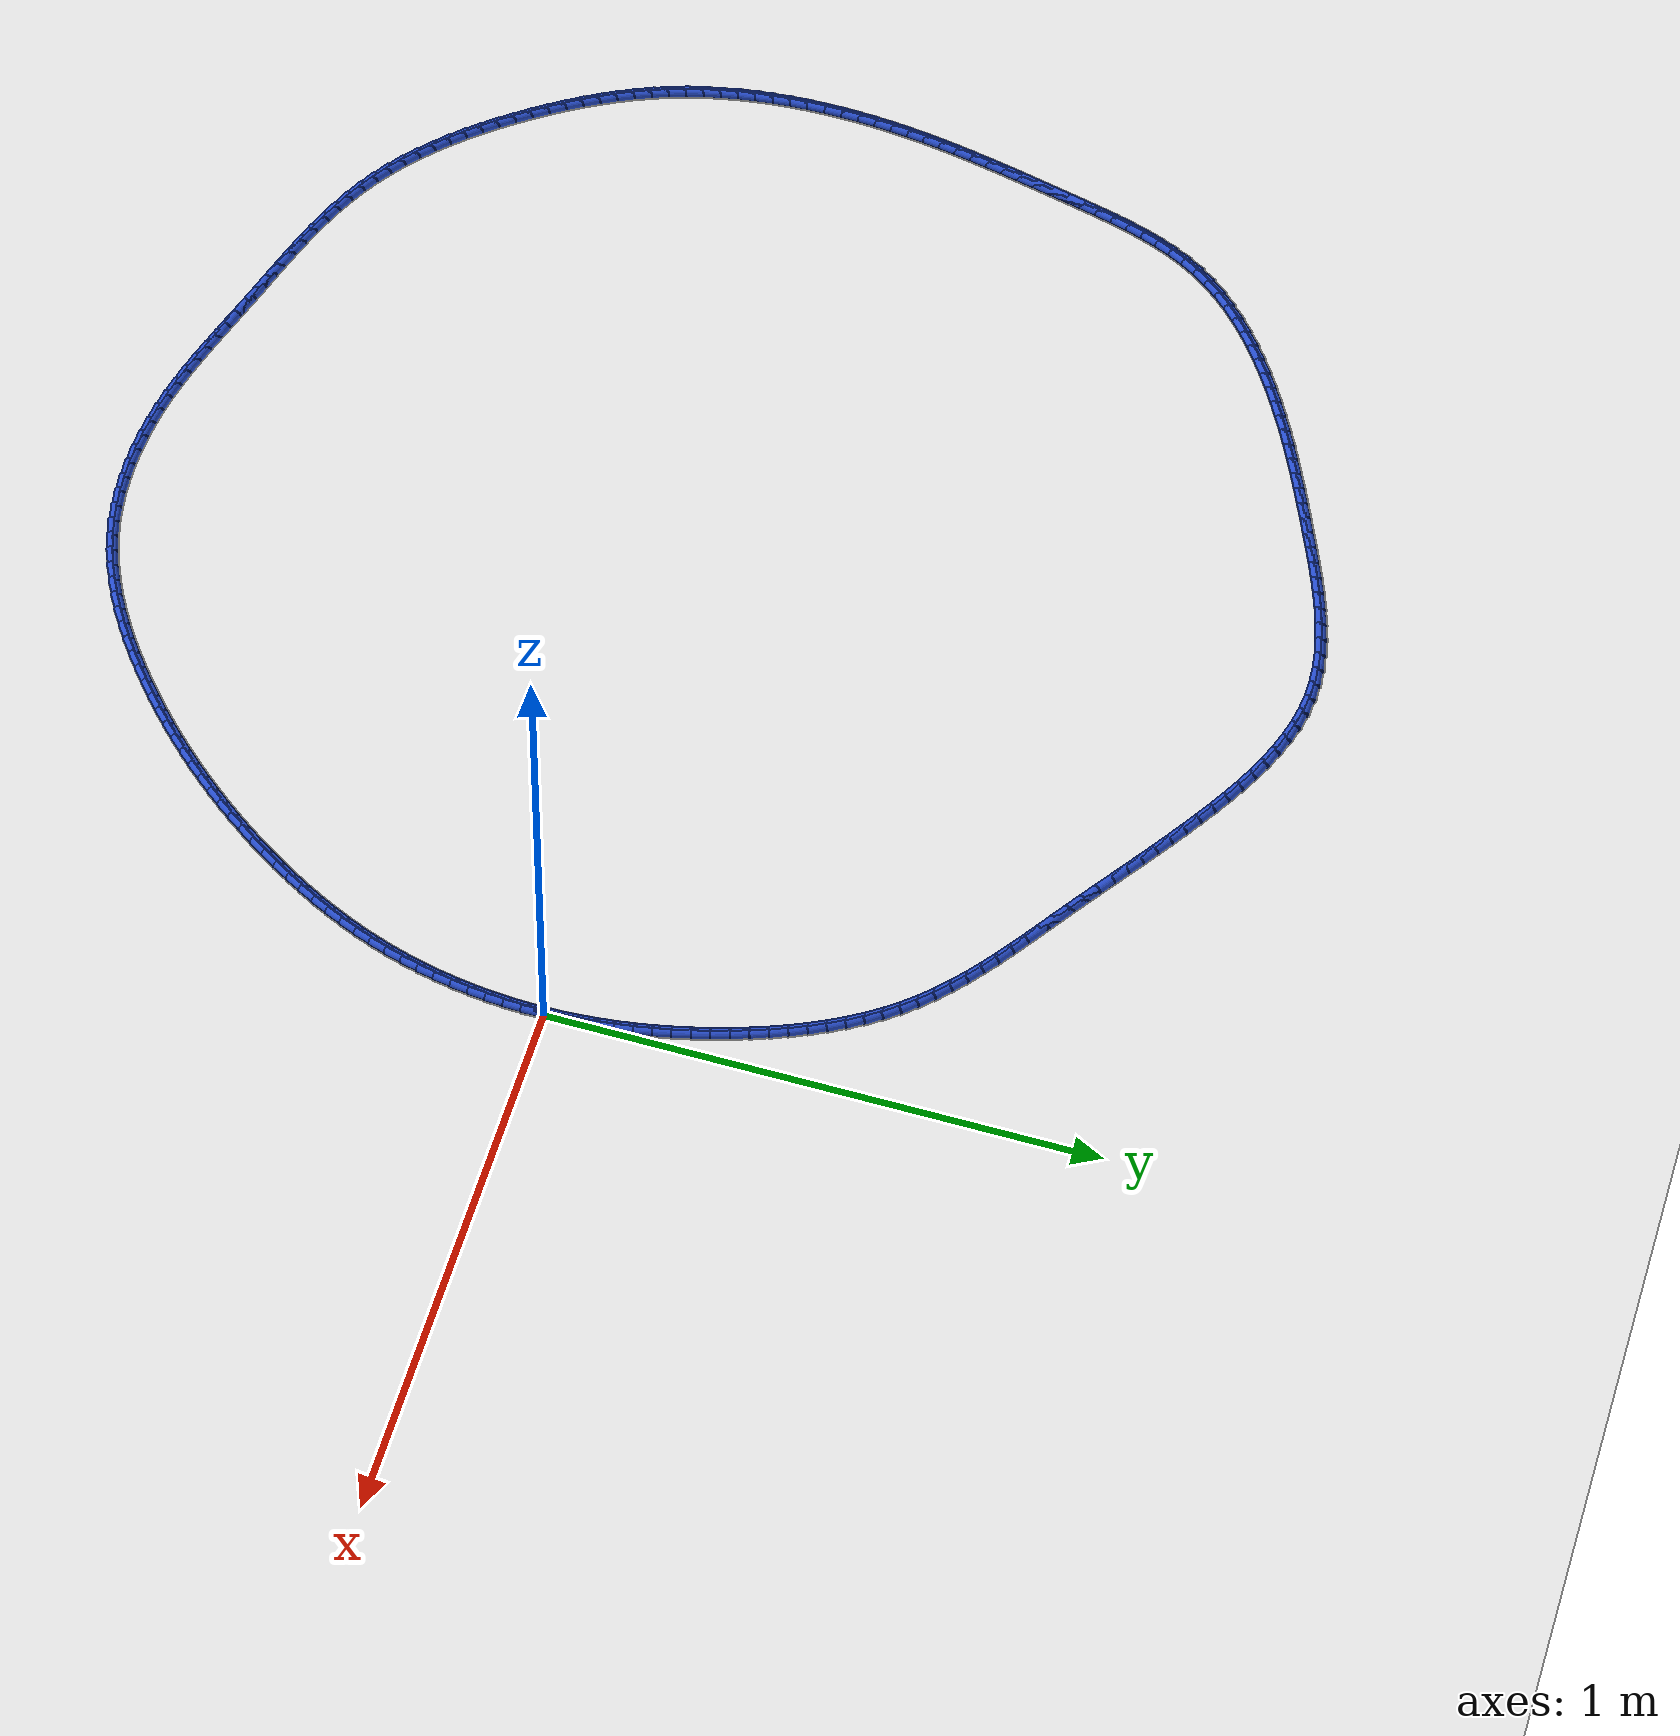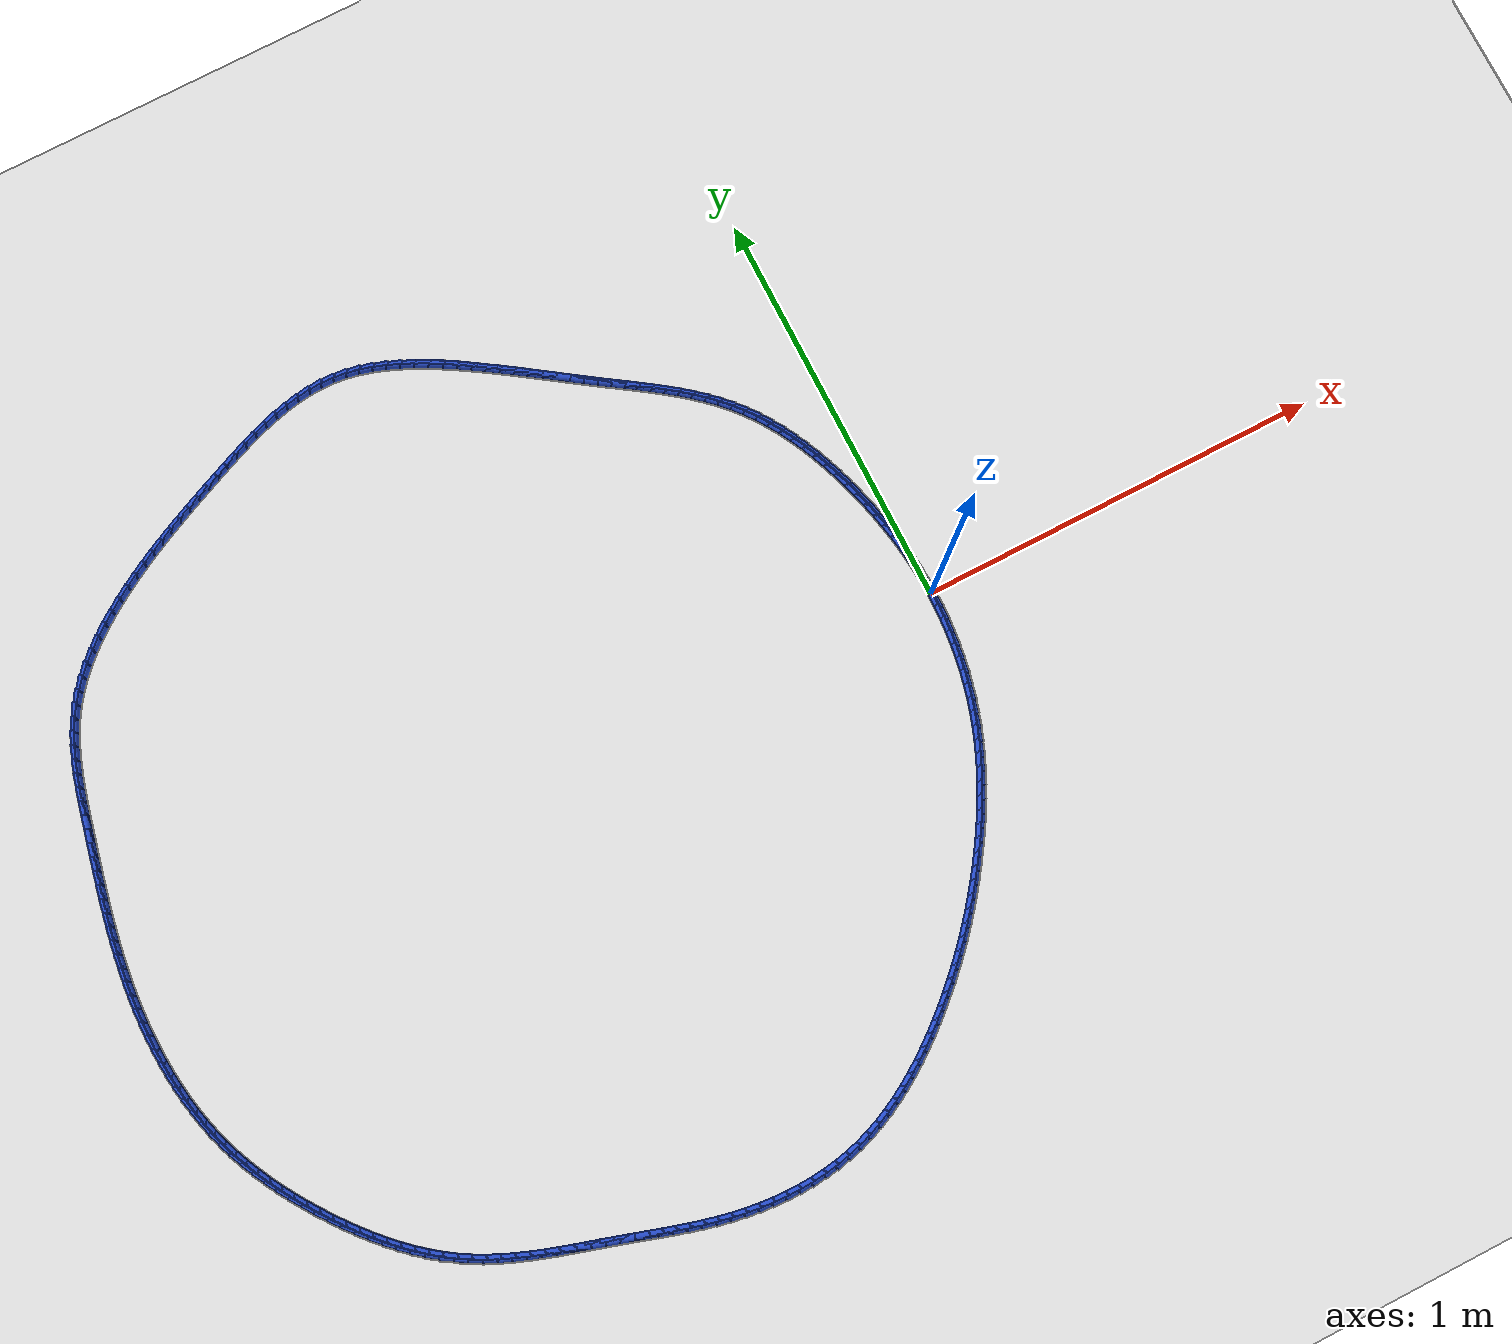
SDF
<sdf version="1.6">
 <world name="default">
  <light name="sun" type="directional">
   <pose>0 0 10 0 -0 0</pose>
   <diffuse>0.8 0.8 0.8 1</diffuse>
   <specular>0.2 0.2 0.2 1</specular>
   <attenuation>
    <range>1000</range>
    <constant>0.9</constant>
    <linear>0.01</linear>
    <quadratic>0.001</quadratic>
   </attenuation>
   <direction>-0.5 0.1 -0.9</direction>
  </light>
  <model name="ground_plane">
   <static>1</static>
   <link name="link">
    <collision name="collision">
     <geometry><plane><normal>0 0 1</normal><size>100 100</size></plane></geometry>
     <surface><friction><ode><mu>100</mu><mu2>50</mu2></ode></friction></surface>
    </collision>
    <visual name="visual">
     <cast_shadows>0</cast_shadows>
     <geometry><plane><normal>0 0 1</normal><size>100 100</size></plane></geometry>
     <material>
      <script><uri>file://media/materials/scripts/gazebo.material</uri><name>Gazebo/WhiteGlow</name></script>
     </material>
    </visual>
   </link>
  </model>
  <gravity>0 0 -9.8</gravity>
  <magnetic_field>6e-06 2.3e-05 -4.2e-05</magnetic_field>
  <atmosphere type="adiabatic"/>
  <physics name="default_physics" default="0" type="ode">
   <max_step_size>0.001</max_step_size>
   <real_time_factor>1</real_time_factor>
   <real_time_update_rate>1000</real_time_update_rate>
  </physics>
  <scene><ambient>0.4 0.4 0.4 1</ambient><background>0.7 0.7 0.7 1</background><shadows>1</shadows></scene>
  <spherical_coordinates>
   <surface_model>EARTH_WGS84</surface_model>
   <latitude_deg>0</latitude_deg>
   <longitude_deg>0</longitude_deg>
   <elevation>0</elevation>
   <heading_deg>0</heading_deg>
  </spherical_coordinates>
  <model name="line">
   <link name="link_0">
    <pose>-9.540979117872439e-18 2.7755575615628914e-17 0.01 0 1.57 -1.5479299830757318</pose>
    <collision name="collision">
     <geometry><cylinder><radius>0.01</radius><length>0.08</length></cylinder></geometry>
    </collision>
    <visual name="visual">
     <material>
      <script><name>Gazebo/Blue</name><uri>file://media/materials/scripts/gazebo.material</uri></script>
     </material>
     <geometry><cylinder><radius>0.01</radius><length>0.08</length></cylinder></geometry>
    </visual>
   </link>
   <link name="link_1">
    <pose>-0.0007515272353551269 0.03286035828101572 0.01 0 1.57 -1.514508421640906</pose>
    <collision name="collision">
     <geometry><cylinder><radius>0.01</radius><length>0.08</length></cylinder></geometry>
    </collision>
    <visual name="visual">
     <material>
      <script><name>Gazebo/Blue</name><uri>file://media/materials/scripts/gazebo.material</uri></script>
     </material>
     <geometry><cylinder><radius>0.01</radius><length>0.08</length></cylinder></geometry>
    </visual>
   </link>
   <link name="link_2">
    <pose>-0.002598972968361298 0.06564705039313544 0.01 0 1.57 -1.4818363842122964</pose>
    <collision name="collision">
     <geometry><cylinder><radius>0.01</radius><length>0.08</length></cylinder></geometry>
    </collision>
    <visual name="visual">
     <material>
      <script><name>Gazebo/Blue</name><uri>file://media/materials/scripts/gazebo.material</uri></script>
     </material>
     <geometry><cylinder><radius>0.01</radius><length>0.08</length></cylinder></geometry>
    </visual>
   </link>
   <link name="link_3">
    <pose>-0.005516052719334551 0.09835143927020644 0.01 0 1.57 -1.4499525543551033</pose>
    <collision name="collision">
     <geometry><cylinder><radius>0.01</radius><length>0.08</length></cylinder></geometry>
    </collision>
    <visual name="visual">
     <material>
      <script><name>Gazebo/Blue</name><uri>file://media/materials/scripts/gazebo.material</uri></script>
     </material>
     <geometry><cylinder><radius>0.01</radius><length>0.08</length></cylinder></geometry>
    </visual>
   </link>
   <link name="link_4">
    <pose>-0.009476482008590892 0.13096488784607593 0.01 0 1.57 -1.4188873814097889</pose>
    <collision name="collision">
     <geometry><cylinder><radius>0.01</radius><length>0.08</length></cylinder></geometry>
    </collision>
    <visual name="visual">
     <material>
      <script><name>Gazebo/Blue</name><uri>file://media/materials/scripts/gazebo.material</uri></script>
     </material>
     <geometry><cylinder><radius>0.01</radius><length>0.08</length></cylinder></geometry>
    </visual>
   </link>
   <link name="link_5">
    <pose>-0.014453976356446343 0.1634787590545911 0.01 0 1.57 -1.3886634785120313</pose>
    <collision name="collision">
     <geometry><cylinder><radius>0.01</radius><length>0.08</length></cylinder></geometry>
    </collision>
    <visual name="visual">
     <material>
      <script><name>Gazebo/Blue</name><uri>file://media/materials/scripts/gazebo.material</uri></script>
     </material>
     <geometry><cylinder><radius>0.01</radius><length>0.08</length></cylinder></geometry>
    </visual>
   </link>
   <link name="link_6">
    <pose>-0.020422251283216918 0.19588441582959926 0.01 0 1.57 -1.3592961373803927</pose>
    <collision name="collision">
     <geometry><cylinder><radius>0.01</radius><length>0.08</length></cylinder></geometry>
    </collision>
    <visual name="visual">
     <material>
      <script><name>Gazebo/Blue</name><uri>file://media/materials/scripts/gazebo.material</uri></script>
     </material>
     <geometry><cylinder><radius>0.01</radius><length>0.08</length></cylinder></geometry>
    </visual>
   </link>
   <link name="link_7">
    <pose>-0.027355022309218647 0.22817322110494767 0.01 0 1.57 -1.3307939262878807</pose>
    <collision name="collision">
     <geometry><cylinder><radius>0.01</radius><length>0.08</length></cylinder></geometry>
    </collision>
    <visual name="visual">
     <material>
      <script><name>Gazebo/Blue</name><uri>file://media/materials/scripts/gazebo.material</uri></script>
     </material>
     <geometry><cylinder><radius>0.01</radius><length>0.08</length></cylinder></geometry>
    </visual>
   </link>
   <link name="link_8">
    <pose>-0.035226004954767534 0.2603365378144835 0.01 0 1.57 -1.3031593400854422</pose>
    <collision name="collision">
     <geometry><cylinder><radius>0.01</radius><length>0.08</length></cylinder></geometry>
    </collision>
    <visual name="visual">
     <material>
      <script><name>Gazebo/Blue</name><uri>file://media/materials/scripts/gazebo.material</uri></script>
     </material>
     <geometry><cylinder><radius>0.01</radius><length>0.08</length></cylinder></geometry>
    </visual>
   </link>
   <link name="link_9">
    <pose>-0.04400891474017961 0.292365728892054 0.01 0 1.57 -1.276328577495393</pose>
    <collision name="collision">
     <geometry><cylinder><radius>0.01</radius><length>0.08</length></cylinder></geometry>
    </collision>
    <visual name="visual">
     <material>
      <script><name>Gazebo/Blue</name><uri>file://media/materials/scripts/gazebo.material</uri></script>
     </material>
     <geometry><cylinder><radius>0.01</radius><length>0.08</length></cylinder></geometry>
    </visual>
   </link>
   <link name="link_10">
    <pose>-0.053679000038851725 0.3242502201008272 0.01 0 1.57 -1.2487136486865247</pose>
    <collision name="collision">
     <geometry><cylinder><radius>0.01</radius><length>0.08</length></cylinder></geometry>
    </collision>
    <visual name="visual">
     <material>
      <script><name>Gazebo/Blue</name><uri>file://media/materials/scripts/gazebo.material</uri></script>
     </material>
     <geometry><cylinder><radius>0.01</radius><length>0.08</length></cylinder></geometry>
    </visual>
   </link>
   <link name="link_11">
    <pose>-0.06425062145098712 0.35593000842314804 0.01 0 1.57 -1.2185306978952686</pose>
    <collision name="collision">
     <geometry><cylinder><radius>0.01</radius><length>0.08</length></cylinder></geometry>
    </collision>
    <visual name="visual">
     <material>
      <script><name>Gazebo/Blue</name><uri>file://media/materials/scripts/gazebo.material</uri></script>
     </material>
     <geometry><cylinder><radius>0.01</radius><length>0.08</length></cylinder></geometry>
    </visual>
   </link>
   <link name="link_12">
    <pose>-0.07577952248550499 0.3872927924453925 0.01 0 1.57 -1.1855185822800796</pose>
    <collision name="collision">
     <geometry><cylinder><radius>0.01</radius><length>0.08</length></cylinder></geometry>
    </collision>
    <visual name="visual">
     <material>
      <script><name>Gazebo/Blue</name><uri>file://media/materials/scripts/gazebo.material</uri></script>
     </material>
     <geometry><cylinder><radius>0.01</radius><length>0.08</length></cylinder></geometry>
    </visual>
   </link>
   <link name="link_13">
    <pose>-0.08832343409421409 0.418223759087202 0.01 0 1.57 -1.1494843146660079</pose>
    <collision name="collision">
     <geometry><cylinder><radius>0.01</radius><length>0.08</length></cylinder></geometry>
    </collision>
    <visual name="visual">
     <material>
      <script><name>Gazebo/Blue</name><uri>file://media/materials/scripts/gazebo.material</uri></script>
     </material>
     <geometry><cylinder><radius>0.01</radius><length>0.08</length></cylinder></geometry>
    </visual>
   </link>
   <link name="link_14">
    <pose>-0.10194008722892318 0.44860809526821804 0.01 0 1.57 -1.1102304231522242</pose>
    <collision name="collision">
     <geometry><cylinder><radius>0.01</radius><length>0.08</length></cylinder></geometry>
    </collision>
    <visual name="visual">
     <material>
      <script><name>Gazebo/Blue</name><uri>file://media/materials/scripts/gazebo.material</uri></script>
     </material>
     <geometry><cylinder><radius>0.01</radius><length>0.08</length></cylinder></geometry>
    </visual>
   </link>
   <link name="link_15">
    <pose>-0.11668721284144098 0.47833098790808176 0.01 0 1.57 -1.067563860604038</pose>
    <collision name="collision">
     <geometry><cylinder><radius>0.01</radius><length>0.08</length></cylinder></geometry>
    </collision>
    <visual name="visual">
     <material>
      <script><name>Gazebo/Blue</name><uri>file://media/materials/scripts/gazebo.material</uri></script>
     </material>
     <geometry><cylinder><radius>0.01</radius><length>0.08</length></cylinder></geometry>
    </visual>
   </link>
   <link name="link_16">
    <pose>-0.13262254188357628 0.5072776239264348 0.01 0 1.57 -1.0213081383237024</pose>
    <collision name="collision">
     <geometry><cylinder><radius>0.01</radius><length>0.08</length></cylinder></geometry>
    </collision>
    <visual name="visual">
     <material>
      <script><name>Gazebo/Blue</name><uri>file://media/materials/scripts/gazebo.material</uri></script>
     </material>
     <geometry><cylinder><radius>0.01</radius><length>0.08</length></cylinder></geometry>
    </visual>
   </link>
   <link name="link_17">
    <pose>-0.14980380530713783 0.5353331902429186 0.01 0 1.57 -0.9713191868171644</pose>
    <collision name="collision">
     <geometry><cylinder><radius>0.01</radius><length>0.08</length></cylinder></geometry>
    </collision>
    <visual name="visual">
     <material>
      <script><name>Gazebo/Blue</name><uri>file://media/materials/scripts/gazebo.material</uri></script>
     </material>
     <geometry><cylinder><radius>0.01</radius><length>0.08</length></cylinder></geometry>
    </visual>
   </link>
   <link name="link_18">
    <pose>-0.1682887340639343 0.5623828737771742 0.01 0 1.57 -0.9175050932684928</pose>
    <collision name="collision">
     <geometry><cylinder><radius>0.01</radius><length>0.08</length></cylinder></geometry>
    </collision>
    <visual name="visual">
     <material>
      <script><name>Gazebo/Blue</name><uri>file://media/materials/scripts/gazebo.material</uri></script>
     </material>
     <geometry><cylinder><radius>0.01</radius><length>0.08</length></cylinder></geometry>
    </visual>
   </link>
   <link name="link_19">
    <pose>-0.1881350591057746 0.5883118614488434 0.01 0 1.57 -0.860006029595551</pose>
    <collision name="collision">
     <geometry><cylinder><radius>0.01</radius><length>0.08</length></cylinder></geometry>
    </collision>
    <visual name="visual">
     <material>
      <script><name>Gazebo/Blue</name><uri>file://media/materials/scripts/gazebo.material</uri></script>
     </material>
     <geometry><cylinder><radius>0.01</radius><length>0.08</length></cylinder></geometry>
    </visual>
   </link>
   <link name="link_20">
    <pose>-0.20939704883201216 0.6130091513345207 0.01 0 1.57 -0.803554375496242</pose>
    <collision name="collision">
     <geometry><cylinder><radius>0.01</radius><length>0.08</length></cylinder></geometry>
    </collision>
    <visual name="visual">
     <material>
      <script><name>Gazebo/Blue</name><uri>file://media/materials/scripts/gazebo.material</uri></script>
     </material>
     <geometry><cylinder><radius>0.01</radius><length>0.08</length></cylinder></geometry>
    </visual>
   </link>
   <link name="link_21">
    <pose>-0.23202692477752082 0.6364760622978917 0.01 0 1.57 -0.7536377840492777</pose>
    <collision name="collision">
     <geometry><cylinder><radius>0.01</radius><length>0.08</length></cylinder></geometry>
    </collision>
    <visual name="visual">
     <material>
      <script><name>Gazebo/Blue</name><uri>file://media/materials/scripts/gazebo.material</uri></script>
     </material>
     <geometry><cylinder><radius>0.01</radius><length>0.08</length></cylinder></geometry>
    </visual>
   </link>
   <link name="link_22">
    <pose>-0.25586060120928383 0.6588419301088015 0.01 0 1.57 -0.7106281662134715</pose>
    <collision name="collision">
     <geometry><cylinder><radius>0.01</radius><length>0.08</length></cylinder></geometry>
    </collision>
    <visual name="visual">
     <material>
      <script><name>Gazebo/Blue</name><uri>file://media/materials/scripts/gazebo.material</uri></script>
     </material>
     <geometry><cylinder><radius>0.01</radius><length>0.08</length></cylinder></geometry>
    </visual>
   </link>
   <link name="link_23">
    <pose>-0.2807276624553696 0.6802430577646006 0.01 0 1.57 -0.6744722932389033</pose>
    <collision name="collision">
     <geometry><cylinder><radius>0.01</radius><length>0.08</length></cylinder></geometry>
    </collision>
    <visual name="visual">
     <material>
      <script><name>Gazebo/Blue</name><uri>file://media/materials/scripts/gazebo.material</uri></script>
     </material>
     <geometry><cylinder><radius>0.01</radius><length>0.08</length></cylinder></geometry>
    </visual>
   </link>
   <link name="link_24">
    <pose>-0.306457692843847 0.7008157482626399 0.01 0 1.57 -0.6450402758384357</pose>
    <collision name="collision">
     <geometry><cylinder><radius>0.01</radius><length>0.08</length></cylinder></geometry>
    </collision>
    <visual name="visual">
     <material>
      <script><name>Gazebo/Blue</name><uri>file://media/materials/scripts/gazebo.material</uri></script>
     </material>
     <geometry><cylinder><radius>0.01</radius><length>0.08</length></cylinder></geometry>
    </visual>
   </link>
   <link name="link_25">
    <pose>-0.3328802767027845 0.7206963046002702 0.01 0 1.57 -0.6221758415268458</pose>
    <collision name="collision">
     <geometry><cylinder><radius>0.01</radius><length>0.08</length></cylinder></geometry>
    </collision>
    <visual name="visual">
     <material>
      <script><name>Gazebo/Blue</name><uri>file://media/materials/scripts/gazebo.material</uri></script>
     </material>
     <geometry><cylinder><radius>0.01</radius><length>0.08</length></cylinder></geometry>
    </visual>
   </link>
   <link name="link_26">
    <pose>-0.35982499836025095 0.740021029774843 0.01 0 1.57 -0.6057343149471346</pose>
    <collision name="collision">
     <geometry><cylinder><radius>0.01</radius><length>0.08</length></cylinder></geometry>
    </collision>
    <visual name="visual">
     <material>
      <script><name>Gazebo/Blue</name><uri>file://media/materials/scripts/gazebo.material</uri></script>
     </material>
     <geometry><cylinder><radius>0.01</radius><length>0.08</length></cylinder></geometry>
    </visual>
   </link>
   <link name="link_27">
    <pose>-0.38712144214431476 0.7589262267837081 0.01 0 1.57 -0.5956097127152926</pose>
    <collision name="collision">
     <geometry><cylinder><radius>0.01</radius><length>0.08</length></cylinder></geometry>
    </collision>
    <visual name="visual">
     <material>
      <script><name>Gazebo/Blue</name><uri>file://media/materials/scripts/gazebo.material</uri></script>
     </material>
     <geometry><cylinder><radius>0.01</radius><length>0.08</length></cylinder></geometry>
    </visual>
   </link>
   <link name="link_28">
    <pose>-0.41459919238304455 0.777548198624217 0.01 0 1.57 -0.5917530622940216</pose>
    <collision name="collision">
     <geometry><cylinder><radius>0.01</radius><length>0.08</length></cylinder></geometry>
    </collision>
    <visual name="visual">
     <material>
      <script><name>Gazebo/Blue</name><uri>file://media/materials/scripts/gazebo.material</uri></script>
     </material>
     <geometry><cylinder><radius>0.01</radius><length>0.08</length></cylinder></geometry>
    </visual>
   </link>
   <link name="link_29">
    <pose>-0.4420878334045092 0.7960232482937206 0.01 0 1.57 -0.5941732780528943</pose>
    <collision name="collision">
     <geometry><cylinder><radius>0.01</radius><length>0.08</length></cylinder></geometry>
    </collision>
    <visual name="visual">
     <material>
      <script><name>Gazebo/Blue</name><uri>file://media/materials/scripts/gazebo.material</uri></script>
     </material>
     <geometry><cylinder><radius>0.01</radius><length>0.08</length></cylinder></geometry>
    </visual>
   </link>
   <link name="link_30">
    <pose>-0.46941726918743887 0.8144874741246306 0.01 0 1.57 -0.6005097237125809</pose>
    <collision name="collision">
     <geometry><cylinder><radius>0.01</radius><length>0.08</length></cylinder></geometry>
    </collision>
    <visual name="visual">
     <material>
      <script><name>Gazebo/Blue</name><uri>file://media/materials/scripts/gazebo.material</uri></script>
     </material>
     <geometry><cylinder><radius>0.01</radius><length>0.08</length></cylinder></geometry>
    </visual>
   </link>
   <link name="link_31">
    <pose>-0.4964909821055878 0.8330298639017709 0.01 0 1.57 -0.6052269998892688</pose>
    <collision name="collision">
     <geometry><cylinder><radius>0.01</radius><length>0.08</length></cylinder></geometry>
    </collision>
    <visual name="visual">
     <material>
      <script><name>Gazebo/Blue</name><uri>file://media/materials/scripts/gazebo.material</uri></script>
     </material>
     <geometry><cylinder><radius>0.01</radius><length>0.08</length></cylinder></geometry>
    </visual>
   </link>
   <link name="link_32">
    <pose>-0.5233795682869131 0.8516324063313944 0.01 0 1.57 -0.6075108740332876</pose>
    <collision name="collision">
     <geometry><cylinder><radius>0.01</radius><length>0.08</length></cylinder></geometry>
    </collision>
    <visual name="visual">
     <material>
      <script><name>Gazebo/Blue</name><uri>file://media/materials/scripts/gazebo.material</uri></script>
     </material>
     <geometry><cylinder><radius>0.01</radius><length>0.08</length></cylinder></geometry>
    </visual>
   </link>
   <link name="link_33">
    <pose>-0.5501766999237757 0.8702623150484877 0.01 0 1.57 -0.6073357224820237</pose>
    <collision name="collision">
     <geometry><cylinder><radius>0.01</radius><length>0.08</length></cylinder></geometry>
    </collision>
    <visual name="visual">
     <material>
      <script><name>Gazebo/Blue</name><uri>file://media/materials/scripts/gazebo.material</uri></script>
     </material>
     <geometry><cylinder><radius>0.01</radius><length>0.08</length></cylinder></geometry>
    </visual>
   </link>
   <link name="link_34">
    <pose>-0.576976049208537 0.8888868036880374 0.01 0 1.57 -0.6047021967439316</pose>
    <collision name="collision">
     <geometry><cylinder><radius>0.01</radius><length>0.08</length></cylinder></geometry>
    </collision>
    <visual name="visual">
     <material>
      <script><name>Gazebo/Blue</name><uri>file://media/materials/scripts/gazebo.material</uri></script>
     </material>
     <geometry><cylinder><radius>0.01</radius><length>0.08</length></cylinder></geometry>
    </visual>
   </link>
   <link name="link_35">
    <pose>-0.6038712883335569 0.907473085885029 0.01 0 1.57 -0.5996372483421207</pose>
    <collision name="collision">
     <geometry><cylinder><radius>0.01</radius><length>0.08</length></cylinder></geometry>
    </collision>
    <visual name="visual">
     <material>
      <script><name>Gazebo/Blue</name><uri>file://media/materials/scripts/gazebo.material</uri></script>
     </material>
     <geometry><cylinder><radius>0.01</radius><length>0.08</length></cylinder></geometry>
    </visual>
   </link>
   <link name="link_36">
    <pose>-0.6309560894911962 0.9259883752744485 0.01 0 1.57 -0.5921938842149779</pose>
    <collision name="collision">
     <geometry><cylinder><radius>0.01</radius><length>0.08</length></cylinder></geometry>
    </collision>
    <visual name="visual">
     <material>
      <script><name>Gazebo/Blue</name><uri>file://media/materials/scripts/gazebo.material</uri></script>
     </material>
     <geometry><cylinder><radius>0.01</radius><length>0.08</length></cylinder></geometry>
    </visual>
   </link>
   <link name="link_37">
    <pose>-0.6583241248738165 0.944399885491283 0.01 0 1.57 -0.5824506203060552</pose>
    <collision name="collision">
     <geometry><cylinder><radius>0.01</radius><length>0.08</length></cylinder></geometry>
    </collision>
    <visual name="visual">
     <material>
      <script><name>Gazebo/Blue</name><uri>file://media/materials/scripts/gazebo.material</uri></script>
     </material>
     <geometry><cylinder><radius>0.01</radius><length>0.08</length></cylinder></geometry>
    </visual>
   </link>
   <link name="link_38">
    <pose>-0.6860690666737779 0.9626748301705175 0.01 0 1.57 -0.570480470619888</pose>
    <collision name="collision">
     <geometry><cylinder><radius>0.01</radius><length>0.08</length></cylinder></geometry>
    </collision>
    <visual name="visual">
     <material>
      <script><name>Gazebo/Blue</name><uri>file://media/materials/scripts/gazebo.material</uri></script>
     </material>
     <geometry><cylinder><radius>0.01</radius><length>0.08</length></cylinder></geometry>
    </visual>
   </link>
   <link name="link_39">
    <pose>-0.7142835359607912 0.9807785492517747 0.01 0 1.57 -0.5549319335862585</pose>
    <collision name="collision">
     <geometry><cylinder><radius>0.01</radius><length>0.08</length></cylinder></geometry>
    </collision>
    <visual name="visual">
     <material>
      <script><name>Gazebo/Blue</name><uri>file://media/materials/scripts/gazebo.material</uri></script>
     </material>
     <geometry><cylinder><radius>0.01</radius><length>0.08</length></cylinder></geometry>
    </visual>
   </link>
   <link name="link_40">
    <pose>-0.7430095182004149 0.9985861213747973 0.01 0 1.57 -0.5336857095382176</pose>
    <collision name="collision">
     <geometry><cylinder><radius>0.01</radius><length>0.08</length></cylinder></geometry>
    </collision>
    <visual name="visual">
     <material>
      <script><name>Gazebo/Blue</name><uri>file://media/materials/scripts/gazebo.material</uri></script>
     </material>
     <geometry><cylinder><radius>0.01</radius><length>0.08</length></cylinder></geometry>
    </visual>
   </link>
   <link name="link_41">
    <pose>-0.7722169324519302 1.0158441620629637 0.01 0 1.57 -0.5063580423142789</pose>
    <collision name="collision">
     <geometry><cylinder><radius>0.01</radius><length>0.08</length></cylinder></geometry>
    </collision>
    <visual name="visual">
     <material>
      <script><name>Gazebo/Blue</name><uri>file://media/materials/scripts/gazebo.material</uri></script>
     </material>
     <geometry><cylinder><radius>0.01</radius><length>0.08</length></cylinder></geometry>
    </visual>
   </link>
   <link name="link_42">
    <pose>-0.8018701924237545 1.0322894731890886 0.01 0 1.57 -0.47259146949367226</pose>
    <collision name="collision">
     <geometry><cylinder><radius>0.01</radius><length>0.08</length></cylinder></geometry>
    </collision>
    <visual name="visual">
     <material>
      <script><name>Gazebo/Blue</name><uri>file://media/materials/scripts/gazebo.material</uri></script>
     </material>
     <geometry><cylinder><radius>0.01</radius><length>0.08</length></cylinder></geometry>
    </visual>
   </link>
   <link name="link_43">
    <pose>-0.8319337118243044 1.0476588566259866 0.01 0 1.57 -0.4319163879325621</pose>
    <collision name="collision">
     <geometry><cylinder><radius>0.01</radius><length>0.08</length></cylinder></geometry>
    </collision>
    <visual name="visual">
     <material>
      <script><name>Gazebo/Blue</name><uri>file://media/materials/scripts/gazebo.material</uri></script>
     </material>
     <geometry><cylinder><radius>0.01</radius><length>0.08</length></cylinder></geometry>
    </visual>
   </link>
   <link name="link_44">
    <pose>-0.8623719043619977 1.0616891142464717 0.01 0 1.57 -0.3837798476056508</pose>
    <collision name="collision">
     <geometry><cylinder><radius>0.01</radius><length>0.08</length></cylinder></geometry>
    </collision>
    <visual name="visual">
     <material>
      <script><name>Gazebo/Blue</name><uri>file://media/materials/scripts/gazebo.material</uri></script>
     </material>
     <geometry><cylinder><radius>0.01</radius><length>0.08</length></cylinder></geometry>
    </visual>
   </link>
   <link name="link_45">
    <pose>-0.8931491837452515 1.0741170479233588 0.01 0 1.57 -0.3275927530733358</pose>
    <collision name="collision">
     <geometry><cylinder><radius>0.01</radius><length>0.08</length></cylinder></geometry>
    </collision>
    <visual name="visual">
     <material>
      <script><name>Gazebo/Blue</name><uri>file://media/materials/scripts/gazebo.material</uri></script>
     </material>
     <geometry><cylinder><radius>0.01</radius><length>0.08</length></cylinder></geometry>
    </visual>
   </link>
   <link name="link_46">
    <pose>-0.9242299636824829 1.084679459529462 0.01 0 1.57 -0.2628061006002471</pose>
    <collision name="collision">
     <geometry><cylinder><radius>0.01</radius><length>0.08</length></cylinder></geometry>
    </collision>
    <visual name="visual">
     <material>
      <script><name>Gazebo/Blue</name><uri>file://media/materials/scripts/gazebo.material</uri></script>
     </material>
     <geometry><cylinder><radius>0.01</radius><length>0.08</length></cylinder></geometry>
    </visual>
   </link>
   <link name="link_47">
    <pose>-0.9555786578821089 1.0931131509375958 0.01 0 1.57 -0.18902623507460303</pose>
    <collision name="collision">
     <geometry><cylinder><radius>0.01</radius><length>0.08</length></cylinder></geometry>
    </collision>
    <visual name="visual">
     <material>
      <script><name>Gazebo/Blue</name><uri>file://media/materials/scripts/gazebo.material</uri></script>
     </material>
     <geometry><cylinder><radius>0.01</radius><length>0.08</length></cylinder></geometry>
    </visual>
   </link>
   <link name="link_48">
    <pose>-0.9871596800525467 1.0991549240205745 0.01 0 1.57 -0.10618507129141638</pose>
    <collision name="collision">
     <geometry><cylinder><radius>0.01</radius><length>0.08</length></cylinder></geometry>
    </collision>
    <visual name="visual">
     <material>
      <script><name>Gazebo/Blue</name><uri>file://media/materials/scripts/gazebo.material</uri></script>
     </material>
     <geometry><cylinder><radius>0.01</radius><length>0.08</length></cylinder></geometry>
    </visual>
   </link>
   <link name="link_49">
    <pose>-1.0189374366607247 1.1025419869664297 0.01 0 1.57 -0.01900978827725867</pose>
    <collision name="collision">
     <geometry><cylinder><radius>0.01</radius><length>0.08</length></cylinder></geometry>
    </collision>
    <visual name="visual">
     <material>
      <script><name>Gazebo/Blue</name><uri>file://media/materials/scripts/gazebo.material</uri></script>
     </material>
     <geometry><cylinder><radius>0.01</radius><length>0.08</length></cylinder></geometry>
    </visual>
   </link>
   <link name="link_50">
    <pose>-1.0508738815127714 1.103149165162234 0.01 0 1.57 0.06109472374575914</pose>
    <collision name="collision">
     <geometry><cylinder><radius>0.01</radius><length>0.08</length></cylinder></geometry>
    </collision>
    <visual name="visual">
     <material>
      <script><name>Gazebo/Blue</name><uri>file://media/materials/scripts/gazebo.material</uri></script>
     </material>
     <geometry><cylinder><radius>0.01</radius><length>0.08</length></cylinder></geometry>
    </visual>
   </link>
   <link name="link_51">
    <pose>-1.082924957124097 1.1011885735994638 0.01 0 1.57 0.13202396310217762</pose>
    <collision name="collision">
     <geometry><cylinder><radius>0.01</radius><length>0.08</length></cylinder></geometry>
    </collision>
    <visual name="visual">
     <material>
      <script><name>Gazebo/Blue</name><uri>file://media/materials/scripts/gazebo.material</uri></script>
     </material>
     <geometry><cylinder><radius>0.01</radius><length>0.08</length></cylinder></geometry>
    </visual>
   </link>
   <link name="link_52">
    <pose>-1.1150457019483202 1.0969230535875685 0.01 0 1.57 0.19375910922811515</pose>
    <collision name="collision">
     <geometry><cylinder><radius>0.01</radius><length>0.08</length></cylinder></geometry>
    </collision>
    <visual name="visual">
     <material>
      <script><name>Gazebo/Blue</name><uri>file://media/materials/scripts/gazebo.material</uri></script>
     </material>
     <geometry><cylinder><radius>0.01</radius><length>0.08</length></cylinder></geometry>
    </visual>
   </link>
   <link name="link_53">
    <pose>-1.1471911544390598 1.090615446435997 0.01 0 1.57 0.24660555343838492</pose>
    <collision name="collision">
     <geometry><cylinder><radius>0.01</radius><length>0.08</length></cylinder></geometry>
    </collision>
    <visual name="visual">
     <material>
      <script><name>Gazebo/Blue</name><uri>file://media/materials/scripts/gazebo.material</uri></script>
     </material>
     <geometry><cylinder><radius>0.01</radius><length>0.08</length></cylinder></geometry>
    </visual>
   </link>
   <link name="link_54">
    <pose>-1.1793163530499342 1.0825285934541986 0.01 0 1.57 0.2910350129425921</pose>
    <collision name="collision">
     <geometry><cylinder><radius>0.01</radius><length>0.08</length></cylinder></geometry>
    </collision>
    <visual name="visual">
     <material>
      <script><name>Gazebo/Blue</name><uri>file://media/materials/scripts/gazebo.material</uri></script>
     </material>
     <geometry><cylinder><radius>0.01</radius><length>0.08</length></cylinder></geometry>
    </visual>
   </link>
   <link name="link_55">
    <pose>-1.2113763362345604 1.072925335951621 0.01 0 1.57 0.3275669802625318</pose>
    <collision name="collision">
     <geometry><cylinder><radius>0.01</radius><length>0.08</length></cylinder></geometry>
    </collision>
    <visual name="visual">
     <material>
      <script><name>Gazebo/Blue</name><uri>file://media/materials/scripts/gazebo.material</uri></script>
     </material>
     <geometry><cylinder><radius>0.01</radius><length>0.08</length></cylinder></geometry>
    </visual>
   </link>
   <link name="link_56">
    <pose>-1.243326142446559 1.062068515237715 0.01 0 1.57 0.3566883613919532</pose>
    <collision name="collision">
     <geometry><cylinder><radius>0.01</radius><length>0.08</length></cylinder></geometry>
    </collision>
    <visual name="visual">
     <material>
      <script><name>Gazebo/Blue</name><uri>file://media/materials/scripts/gazebo.material</uri></script>
     </material>
     <geometry><cylinder><radius>0.01</radius><length>0.08</length></cylinder></geometry>
    </visual>
   </link>
   <link name="link_57">
    <pose>-1.2751208101395468 1.0502209726219283 0.01 0 1.57 0.3788025073321599</pose>
    <collision name="collision">
     <geometry><cylinder><radius>0.01</radius><length>0.08</length></cylinder></geometry>
    </collision>
    <visual name="visual">
     <material>
      <script><name>Gazebo/Blue</name><uri>file://media/materials/scripts/gazebo.material</uri></script>
     </material>
     <geometry><cylinder><radius>0.01</radius><length>0.08</length></cylinder></geometry>
    </visual>
   </link>
   <link name="link_58">
    <pose>-1.3067153777671427 1.03764554941371 0.01 0 1.57 0.39419759387340697</pose>
    <collision name="collision">
     <geometry><cylinder><radius>0.01</radius><length>0.08</length></cylinder></geometry>
    </collision>
    <visual name="visual">
     <material>
      <script><name>Gazebo/Blue</name><uri>file://media/materials/scripts/gazebo.material</uri></script>
     </material>
     <geometry><cylinder><radius>0.01</radius><length>0.08</length></cylinder></geometry>
    </visual>
   </link>
   <link name="link_59">
    <pose>-1.3380648837829656 1.0246050869225096 0.01 0 1.57 0.40302581201148924</pose>
    <collision name="collision">
     <geometry><cylinder><radius>0.01</radius><length>0.08</length></cylinder></geometry>
    </collision>
    <visual name="visual">
     <material>
      <script><name>Gazebo/Blue</name><uri>file://media/materials/scripts/gazebo.material</uri></script>
     </material>
     <geometry><cylinder><radius>0.01</radius><length>0.08</length></cylinder></geometry>
    </visual>
   </link>
   <link name="link_60">
    <pose>-1.3691243666406332 1.0113624264577754 0.01 0 1.57 0.40665078527565607</pose>
    <collision name="collision">
     <geometry><cylinder><radius>0.01</radius><length>0.08</length></cylinder></geometry>
    </collision>
    <visual name="visual">
     <material>
      <script><name>Gazebo/Blue</name><uri>file://media/materials/scripts/gazebo.material</uri></script>
     </material>
     <geometry><cylinder><radius>0.01</radius><length>0.08</length></cylinder></geometry>
    </visual>
   </link>
   <link name="link_61">
    <pose>-1.3998582252499585 0.9981267340602188 0.01 0 1.57 0.411070220496507</pose>
    <collision name="collision">
     <geometry><cylinder><radius>0.01</radius><length>0.08</length></cylinder></geometry>
    </collision>
    <visual name="visual">
     <material>
      <script><name>Gazebo/Blue</name><uri>file://media/materials/scripts/gazebo.material</uri></script>
     </material>
     <geometry><cylinder><radius>0.01</radius><length>0.08</length></cylinder></geometry>
    </visual>
   </link>
   <link name="link_62">
    <pose>-1.430272380800815 0.9848690763131025 0.01 0 1.57 0.41798846260027633</pose>
    <collision name="collision">
     <geometry><cylinder><radius>0.01</radius><length>0.08</length></cylinder></geometry>
    </collision>
    <visual name="visual">
     <material>
      <script><name>Gazebo/Blue</name><uri>file://media/materials/scripts/gazebo.material</uri></script>
     </material>
     <geometry><cylinder><radius>0.01</radius><length>0.08</length></cylinder></geometry>
    </visual>
   </link>
   <link name="link_63">
    <pose>-1.4603842639430518 0.9714945215893146 0.01 0 1.57 0.42742297531845763</pose>
    <collision name="collision">
     <geometry><cylinder><radius>0.01</radius><length>0.08</length></cylinder></geometry>
    </collision>
    <visual name="visual">
     <material>
      <script><name>Gazebo/Blue</name><uri>file://media/materials/scripts/gazebo.material</uri></script>
     </material>
     <geometry><cylinder><radius>0.01</radius><length>0.08</length></cylinder></geometry>
    </visual>
   </link>
   <link name="link_64">
    <pose>-1.4902113057519284 0.9579081358223225 0.01 0 1.57 0.43936432452164415</pose>
    <collision name="collision">
     <geometry><cylinder><radius>0.01</radius><length>0.08</length></cylinder></geometry>
    </collision>
    <visual name="visual">
     <material>
      <script><name>Gazebo/Blue</name><uri>file://media/materials/scripts/gazebo.material</uri></script>
     </material>
     <geometry><cylinder><radius>0.01</radius><length>0.08</length></cylinder></geometry>
    </visual>
   </link>
   <link name="link_65">
    <pose>-1.5197709373027033 0.9440149849455926 0.01 0 1.57 0.45377395870528564</pose>
    <collision name="collision">
     <geometry><cylinder><radius>0.01</radius><length>0.08</length></cylinder></geometry>
    </collision>
    <visual name="visual">
     <material>
      <script><name>Gazebo/Blue</name><uri>file://media/materials/scripts/gazebo.material</uri></script>
     </material>
     <geometry><cylinder><radius>0.01</radius><length>0.08</length></cylinder></geometry>
    </visual>
   </link>
   <link name="link_66">
    <pose>-1.5490805896706377 0.9297201348925915 0.01 0 1.57 0.47058227792671764</pose>
    <collision name="collision">
     <geometry><cylinder><radius>0.01</radius><length>0.08</length></cylinder></geometry>
    </collision>
    <visual name="visual">
     <material>
      <script><name>Gazebo/Blue</name><uri>file://media/materials/scripts/gazebo.material</uri></script>
     </material>
     <geometry><cylinder><radius>0.01</radius><length>0.08</length></cylinder></geometry>
    </visual>
   </link>
   <link name="link_67">
    <pose>-1.5781576939309907 0.9149286515967868 0.01 0 1.57 0.4896872897319653</pose>
    <collision name="collision">
     <geometry><cylinder><radius>0.01</radius><length>0.08</length></cylinder></geometry>
    </collision>
    <visual name="visual">
     <material>
      <script><name>Gazebo/Blue</name><uri>file://media/materials/scripts/gazebo.material</uri></script>
     </material>
     <geometry><cylinder><radius>0.01</radius><length>0.08</length></cylinder></geometry>
    </visual>
   </link>
   <link name="link_68">
    <pose>-1.6070196811590216 0.8995456009916449 0.01 0 1.57 0.51095411464108</pose>
    <collision name="collision">
     <geometry><cylinder><radius>0.01</radius><length>0.08</length></cylinder></geometry>
    </collision>
    <visual name="visual">
     <material>
      <script><name>Gazebo/Blue</name><uri>file://media/materials/scripts/gazebo.material</uri></script>
     </material>
     <geometry><cylinder><radius>0.01</radius><length>0.08</length></cylinder></geometry>
    </visual>
   </link>
   <link name="link_69">
    <pose>-1.6356839824299905 0.8834760490106328 0.01 0 1.57 0.5342158809843386</pose>
    <collision name="collision">
     <geometry><cylinder><radius>0.01</radius><length>0.08</length></cylinder></geometry>
    </collision>
    <visual name="visual">
     <material>
      <script><name>Gazebo/Blue</name><uri>file://media/materials/scripts/gazebo.material</uri></script>
     </material>
     <geometry><cylinder><radius>0.01</radius><length>0.08</length></cylinder></geometry>
    </visual>
   </link>
   <link name="link_70">
    <pose>-1.6641680013082867 0.866625067010155 0.01 0 1.57 0.5598283403920468</pose>
    <collision name="collision">
     <geometry><cylinder><radius>0.01</radius><length>0.08</length></cylinder></geometry>
    </collision>
    <visual name="visual">
     <material>
      <script><name>Gazebo/Blue</name><uri>file://media/materials/scripts/gazebo.material</uri></script>
     </material>
     <geometry><cylinder><radius>0.01</radius><length>0.08</length></cylinder></geometry>
    </visual>
   </link>
   <link name="link_71">
    <pose>-1.6924383648062284 0.8489077354120221 0.01 0 1.57 0.5894820347865831</pose>
    <collision name="collision">
     <geometry><cylinder><radius>0.01</radius><length>0.08</length></cylinder></geometry>
    </collision>
    <visual name="visual">
     <material>
      <script><name>Gazebo/Blue</name><uri>file://media/materials/scripts/gazebo.material</uri></script>
     </material>
     <geometry><cylinder><radius>0.01</radius><length>0.08</length></cylinder></geometry>
    </visual>
   </link>
   <link name="link_72">
    <pose>-1.7203057350199529 0.8302698784160938 0.01 0 1.57 0.6237845769787325</pose>
    <collision name="collision">
     <geometry><cylinder><radius>0.01</radius><length>0.08</length></cylinder></geometry>
    </collision>
    <visual name="visual">
     <material>
      <script><name>Gazebo/Blue</name><uri>file://media/materials/scripts/gazebo.material</uri></script>
     </material>
     <geometry><cylinder><radius>0.01</radius><length>0.08</length></cylinder></geometry>
    </visual>
   </link>
   <link name="link_73">
    <pose>-1.7475509277032315 0.8106632035282172 0.01 0 1.57 0.6631040274777865</pose>
    <collision name="collision">
     <geometry><cylinder><radius>0.01</radius><length>0.08</length></cylinder></geometry>
    </collision>
    <visual name="visual">
     <material>
      <script><name>Gazebo/Blue</name><uri>file://media/materials/scripts/gazebo.material</uri></script>
     </material>
     <geometry><cylinder><radius>0.01</radius><length>0.08</length></cylinder></geometry>
    </visual>
   </link>
   <link name="link_74">
    <pose>-1.7739547586098352 0.7900394182542398 0.01 0 1.57 0.7078608640077166</pose>
    <collision name="collision">
     <geometry><cylinder><radius>0.01</radius><length>0.08</length></cylinder></geometry>
    </collision>
    <visual name="visual">
     <material>
      <script><name>Gazebo/Blue</name><uri>file://media/materials/scripts/gazebo.material</uri></script>
     </material>
     <geometry><cylinder><radius>0.01</radius><length>0.08</length></cylinder></geometry>
    </visual>
   </link>
   <link name="link_75">
    <pose>-1.7992980434935357 0.7683502301000098 0.01 0 1.57 0.7585054186711943</pose>
    <collision name="collision">
     <geometry><cylinder><radius>0.01</radius><length>0.08</length></cylinder></geometry>
    </collision>
    <visual name="visual">
     <material>
      <script><name>Gazebo/Blue</name><uri>file://media/materials/scripts/gazebo.material</uri></script>
     </material>
     <geometry><cylinder><radius>0.01</radius><length>0.08</length></cylinder></geometry>
    </visual>
   </link>
   <link name="link_76">
    <pose>-1.8233615981081028 0.7455473465713736 0.01 0 1.57 0.8154824860852472</pose>
    <collision name="collision">
     <geometry><cylinder><radius>0.01</radius><length>0.08</length></cylinder></geometry>
    </collision>
    <visual name="visual">
     <material>
      <script><name>Gazebo/Blue</name><uri>file://media/materials/scripts/gazebo.material</uri></script>
     </material>
     <geometry><cylinder><radius>0.01</radius><length>0.08</length></cylinder></geometry>
    </visual>
   </link>
   <link name="link_77">
    <pose>-1.8459262382073094 0.7215824751741793 0.01 0 1.57 0.8791781418823175</pose>
    <collision name="collision">
     <geometry><cylinder><radius>0.01</radius><length>0.08</length></cylinder></geometry>
    </collision>
    <visual name="visual">
     <material>
      <script><name>Gazebo/Blue</name><uri>file://media/materials/scripts/gazebo.material</uri></script>
     </material>
     <geometry><cylinder><radius>0.01</radius><length>0.08</length></cylinder></geometry>
    </visual>
   </link>
   <link name="link_78">
    <pose>-1.866772779544926 0.6964073234142744 0.01 0 1.57 0.9498451327724119</pose>
    <collision name="collision">
     <geometry><cylinder><radius>0.01</radius><length>0.08</length></cylinder></geometry>
    </collision>
    <visual name="visual">
     <material>
      <script><name>Gazebo/Blue</name><uri>file://media/materials/scripts/gazebo.material</uri></script>
     </material>
     <geometry><cylinder><radius>0.01</radius><length>0.08</length></cylinder></geometry>
    </visual>
   </link>
   <link name="link_79">
    <pose>-1.8856820378747239 0.6699735987975061 0.01 0 1.57 1.0265497422026193</pose>
    <collision name="collision">
     <geometry><cylinder><radius>0.01</radius><length>0.08</length></cylinder></geometry>
    </collision>
    <visual name="visual">
     <material>
      <script><name>Gazebo/Blue</name><uri>file://media/materials/scripts/gazebo.material</uri></script>
     </material>
     <geometry><cylinder><radius>0.01</radius><length>0.08</length></cylinder></geometry>
    </visual>
   </link>
   <link name="link_80">
    <pose>-1.9024631503951397 0.6422461605799253 0.01 0 1.57 1.0993886387100689</pose>
    <collision name="collision">
     <geometry><cylinder><radius>0.01</radius><length>0.08</length></cylinder></geometry>
    </collision>
    <visual name="visual">
     <material>
      <script><name>Gazebo/Blue</name><uri>file://media/materials/scripts/gazebo.material</uri></script>
     </material>
     <geometry><cylinder><radius>0.01</radius><length>0.08</length></cylinder></geometry>
    </visual>
   </link>
   <link name="link_81">
    <pose>-1.9172074506485233 0.6133209127388967 0.01 0 1.57 1.162405658402163</pose>
    <collision name="collision">
     <geometry><cylinder><radius>0.01</radius><length>0.08</length></cylinder></geometry>
    </collision>
    <visual name="visual">
     <material>
      <script><name>Gazebo/Blue</name><uri>file://media/materials/scripts/gazebo.material</uri></script>
     </material>
     <geometry><cylinder><radius>0.01</radius><length>0.08</length></cylinder></geometry>
    </visual>
   </link>
   <link name="link_82">
    <pose>-1.930168231713936 0.583368969093479 0.01 0 1.57 1.2154452599703611</pose>
    <collision name="collision">
     <geometry><cylinder><radius>0.01</radius><length>0.08</length></cylinder></geometry>
    </collision>
    <visual name="visual">
     <material>
      <script><name>Gazebo/Blue</name><uri>file://media/materials/scripts/gazebo.material</uri></script>
     </material>
     <geometry><cylinder><radius>0.01</radius><length>0.08</length></cylinder></geometry>
    </visual>
   </link>
   <link name="link_83">
    <pose>-1.941600711285096 0.5525623372042585 0.01 0 1.57 1.2587095356892897</pose>
    <collision name="collision">
     <geometry><cylinder><radius>0.01</radius><length>0.08</length></cylinder></geometry>
    </collision>
    <visual name="visual">
     <material>
      <script><name>Gazebo/Blue</name><uri>file://media/materials/scripts/gazebo.material</uri></script>
     </material>
     <geometry><cylinder><radius>0.01</radius><length>0.08</length></cylinder></geometry>
    </visual>
   </link>
   <link name="link_84">
    <pose>-1.9517601070557218 0.5210730246318219 0.01 0 1.57 1.292534903014757</pose>
    <collision name="collision">
     <geometry><cylinder><radius>0.01</radius><length>0.08</length></cylinder></geometry>
    </collision>
    <visual name="visual">
     <material>
      <script><name>Gazebo/Blue</name><uri>file://media/materials/scripts/gazebo.material</uri></script>
     </material>
     <geometry><cylinder><radius>0.01</radius><length>0.08</length></cylinder></geometry>
    </visual>
   </link>
   <link name="link_85">
    <pose>-1.9609016367195329 0.489073038936755 0.01 0 1.57 1.3172732992020897</pose>
    <collision name="collision">
     <geometry><cylinder><radius>0.01</radius><length>0.08</length></cylinder></geometry>
    </collision>
    <visual name="visual">
     <material>
      <script><name>Gazebo/Blue</name><uri>file://media/materials/scripts/gazebo.material</uri></script>
     </material>
     <geometry><cylinder><radius>0.01</radius><length>0.08</length></cylinder></geometry>
    </visual>
   </link>
   <link name="link_86">
    <pose>-1.9692805179702486 0.4567343876796448 0.01 0 1.57 1.333211011170251</pose>
    <collision name="collision">
     <geometry><cylinder><radius>0.01</radius><length>0.08</length></cylinder></geometry>
    </collision>
    <visual name="visual">
     <material>
      <script><name>Gazebo/Blue</name><uri>file://media/materials/scripts/gazebo.material</uri></script>
     </material>
     <geometry><cylinder><radius>0.01</radius><length>0.08</length></cylinder></geometry>
    </visual>
   </link>
   <link name="link_87">
    <pose>-1.9771519685015868 0.42422907842107754 0.01 0 1.57 1.3405168452358298</pose>
    <collision name="collision">
     <geometry><cylinder><radius>0.01</radius><length>0.08</length></cylinder></geometry>
    </collision>
    <visual name="visual">
     <material>
      <script><name>Gazebo/Blue</name><uri>file://media/materials/scripts/gazebo.material</uri></script>
     </material>
     <geometry><cylinder><radius>0.01</radius><length>0.08</length></cylinder></geometry>
    </visual>
   </link>
   <link name="link_88">
    <pose>-1.984771200856566 0.3917291153859846 0.01 0 1.57 1.3412952254703607</pose>
    <collision name="collision">
     <geometry><cylinder><radius>0.01</radius><length>0.08</length></cylinder></geometry>
    </collision>
    <visual name="visual">
     <material>
      <script><name>Gazebo/Blue</name><uri>file://media/materials/scripts/gazebo.material</uri></script>
     </material>
     <geometry><cylinder><radius>0.01</radius><length>0.08</length></cylinder></geometry>
    </visual>
   </link>
   <link name="link_89">
    <pose>-1.9923316628504433 0.35936650322423613 0.01 0 1.57 1.3427809089515228</pose>
    <collision name="collision">
     <geometry><cylinder><radius>0.01</radius><length>0.08</length></cylinder></geometry>
    </collision>
    <visual name="visual">
     <material>
      <script><name>Gazebo/Blue</name><uri>file://media/materials/scripts/gazebo.material</uri></script>
     </material>
     <geometry><cylinder><radius>0.01</radius><length>0.08</length></cylinder></geometry>
    </visual>
   </link>
   <link name="link_90">
    <pose>-1.999811316487156 0.3271336954017702 0.01 0 1.57 1.3465779267250688</pose>
    <collision name="collision">
     <geometry><cylinder><radius>0.01</radius><length>0.08</length></cylinder></geometry>
    </collision>
    <visual name="visual">
     <material>
      <script><name>Gazebo/Blue</name><uri>file://media/materials/scripts/gazebo.material</uri></script>
     </material>
     <geometry><cylinder><radius>0.01</radius><length>0.08</length></cylinder></geometry>
    </visual>
   </link>
   <link name="link_91">
    <pose>-2.007141159115543 0.2949927305132061 0.01 0 1.57 1.3527046173166308</pose>
    <collision name="collision">
     <geometry><cylinder><radius>0.01</radius><length>0.08</length></cylinder></geometry>
    </collision>
    <visual name="visual">
     <material>
      <script><name>Gazebo/Blue</name><uri>file://media/materials/scripts/gazebo.material</uri></script>
     </material>
     <geometry><cylinder><radius>0.01</radius><length>0.08</length></cylinder></geometry>
    </visual>
   </link>
   <link name="link_92">
    <pose>-2.0142521880844404 0.26290564715316295 0.01 0 1.57 1.361169579254887</pose>
    <collision name="collision">
     <geometry><cylinder><radius>0.01</radius><length>0.08</length></cylinder></geometry>
    </collision>
    <visual name="visual">
     <material>
      <script><name>Gazebo/Blue</name><uri>file://media/materials/scripts/gazebo.material</uri></script>
     </material>
     <geometry><cylinder><radius>0.01</radius><length>0.08</length></cylinder></geometry>
    </visual>
   </link>
   <link name="link_93">
    <pose>-2.0210754007426863 0.23083448391625977 0.01 0 1.57 1.3719704647574542</pose>
    <collision name="collision">
     <geometry><cylinder><radius>0.01</radius><length>0.08</length></cylinder></geometry>
    </collision>
    <visual name="visual">
     <material>
      <script><name>Gazebo/Blue</name><uri>file://media/materials/scripts/gazebo.material</uri></script>
     </material>
     <geometry><cylinder><radius>0.01</radius><length>0.08</length></cylinder></geometry>
    </visual>
   </link>
   <link name="link_94">
    <pose>-2.0275417944391183 0.19874127939711578 0.01 0 1.57 1.3850924975192622</pose>
    <collision name="collision">
     <geometry><cylinder><radius>0.01</radius><length>0.08</length></cylinder></geometry>
    </collision>
    <visual name="visual">
     <material>
      <script><name>Gazebo/Blue</name><uri>file://media/materials/scripts/gazebo.material</uri></script>
     </material>
     <geometry><cylinder><radius>0.01</radius><length>0.08</length></cylinder></geometry>
    </visual>
   </link>
   <link name="link_95">
    <pose>-2.0335823665225736 0.16658807219035 0.01 0 1.57 1.4005067685360666</pose>
    <collision name="collision">
     <geometry><cylinder><radius>0.01</radius><length>0.08</length></cylinder></geometry>
    </collision>
    <visual name="visual">
     <material>
      <script><name>Gazebo/Blue</name><uri>file://media/materials/scripts/gazebo.material</uri></script>
     </material>
     <geometry><cylinder><radius>0.01</radius><length>0.08</length></cylinder></geometry>
    </visual>
   </link>
   <link name="link_96">
    <pose>-2.0391281143418896 0.134336900890582 0.01 0 1.57 1.4181683949833093</pose>
    <collision name="collision">
     <geometry><cylinder><radius>0.01</radius><length>0.08</length></cylinder></geometry>
    </collision>
    <visual name="visual">
     <material>
      <script><name>Gazebo/Blue</name><uri>file://media/materials/scripts/gazebo.material</uri></script>
     </material>
     <geometry><cylinder><radius>0.01</radius><length>0.08</length></cylinder></geometry>
    </visual>
   </link>
   <link name="link_97">
    <pose>-2.0441100352459034 0.10194980409243015 0.01 0 1.57 1.4380146603604618</pose>
    <collision name="collision">
     <geometry><cylinder><radius>0.01</radius><length>0.08</length></cylinder></geometry>
    </collision>
    <visual name="visual">
     <material>
      <script><name>Gazebo/Blue</name><uri>file://media/materials/scripts/gazebo.material</uri></script>
     </material>
     <geometry><cylinder><radius>0.01</radius><length>0.08</length></cylinder></geometry>
    </visual>
   </link>
   <link name="link_98">
    <pose>-2.0484591265834537 0.069388820390514 0.01 0 1.57 1.4599597637354234</pose>
    <collision name="collision">
     <geometry><cylinder><radius>0.01</radius><length>0.08</length></cylinder></geometry>
    </collision>
    <visual name="visual">
     <material>
      <script><name>Gazebo/Blue</name><uri>file://media/materials/scripts/gazebo.material</uri></script>
     </material>
     <geometry><cylinder><radius>0.01</radius><length>0.08</length></cylinder></geometry>
    </visual>
   </link>
   <link name="link_99">
    <pose>-2.052106461139097 0.0366163607824665 0.01 0 1.57 1.4836185498284373</pose>
    <collision name="collision">
     <geometry><cylinder><radius>0.01</radius><length>0.08</length></cylinder></geometry>
    </collision>
    <visual name="visual">
     <material>
      <script><name>Gazebo/Blue</name><uri>file://media/materials/scripts/gazebo.material</uri></script>
     </material>
     <geometry><cylinder><radius>0.01</radius><length>0.08</length></cylinder></geometry>
    </visual>
   </link>
   <link name="link_100">
    <pose>-2.0549896836856476 0.003627280156072757 0.01 0 1.57 1.5084908344666583</pose>
    <collision name="collision">
     <geometry><cylinder><radius>0.01</radius><length>0.08</length></cylinder></geometry>
    </collision>
    <visual name="visual">
     <material>
      <script><name>Gazebo/Blue</name><uri>file://media/materials/scripts/gazebo.material</uri></script>
     </material>
     <geometry><cylinder><radius>0.01</radius><length>0.08</length></cylinder></geometry>
    </visual>
   </link>
   <link name="link_101">
    <pose>-2.0570580175692363 -0.02952640673597542 0.01 0 1.57 1.5346175772512671</pose>
    <collision name="collision">
     <geometry><cylinder><radius>0.01</radius><length>0.08</length></cylinder></geometry>
    </collision>
    <visual name="visual">
     <material>
      <script><name>Gazebo/Blue</name><uri>file://media/materials/scripts/gazebo.material</uri></script>
     </material>
     <geometry><cylinder><radius>0.01</radius><length>0.08</length></cylinder></geometry>
    </visual>
   </link>
   <link name="link_102">
    <pose>-2.0582618647114463 -0.06278686687550247 0.01 0 1.57 1.5620974306779905</pose>
    <collision name="collision">
     <geometry><cylinder><radius>0.01</radius><length>0.08</length></cylinder></geometry>
    </collision>
    <visual name="visual">
     <material>
      <script><name>Gazebo/Blue</name><uri>file://media/materials/scripts/gazebo.material</uri></script>
     </material>
     <geometry><cylinder><radius>0.01</radius><length>0.08</length></cylinder></geometry>
    </visual>
   </link>
   <link name="link_103">
    <pose>-2.0585516270338564 -0.09609626724433303 0.01 0 1.57 -1.5505615422788779</pose>
    <collision name="collision">
     <geometry><cylinder><radius>0.01</radius><length>0.08</length></cylinder></geometry>
    </collision>
    <visual name="visual">
     <material>
      <script><name>Gazebo/Blue</name><uri>file://media/materials/scripts/gazebo.material</uri></script>
     </material>
     <geometry><cylinder><radius>0.01</radius><length>0.08</length></cylinder></geometry>
    </visual>
   </link>
   <link name="link_104">
    <pose>-2.05787770645805 -0.12939677482429163 0.01 0 1.57 -1.520072208334712</pose>
    <collision name="collision">
     <geometry><cylinder><radius>0.01</radius><length>0.08</length></cylinder></geometry>
    </collision>
    <visual name="visual">
     <material>
      <script><name>Gazebo/Blue</name><uri>file://media/materials/scripts/gazebo.material</uri></script>
     </material>
     <geometry><cylinder><radius>0.01</radius><length>0.08</length></cylinder></geometry>
    </visual>
   </link>
   <link name="link_105">
    <pose>-2.056190504905607 -0.1626305565972027 0.01 0 1.57 -1.4879256929430271</pose>
    <collision name="collision">
     <geometry><cylinder><radius>0.01</radius><length>0.08</length></cylinder></geometry>
    </collision>
    <visual name="visual">
     <material>
      <script><name>Gazebo/Blue</name><uri>file://media/materials/scripts/gazebo.material</uri></script>
     </material>
     <geometry><cylinder><radius>0.01</radius><length>0.08</length></cylinder></geometry>
    </visual>
   </link>
   <link name="link_106">
    <pose>-2.0534404242981097 -0.195739779544891 0.01 0 1.57 -1.4540227133127657</pose>
    <collision name="collision">
     <geometry><cylinder><radius>0.01</radius><length>0.08</length></cylinder></geometry>
    </collision>
    <visual name="visual">
     <material>
      <script><name>Gazebo/Blue</name><uri>file://media/materials/scripts/gazebo.material</uri></script>
     </material>
     <geometry><cylinder><radius>0.01</radius><length>0.08</length></cylinder></geometry>
    </visual>
   </link>
   <link name="link_107">
    <pose>-2.0495778665571387 -0.22866661064918087 0.01 0 1.57 -1.4182688078830175</pose>
    <collision name="collision">
     <geometry><cylinder><radius>0.01</radius><length>0.08</length></cylinder></geometry>
    </collision>
    <visual name="visual">
     <material>
      <script><name>Gazebo/Blue</name><uri>file://media/materials/scripts/gazebo.material</uri></script>
     </material>
     <geometry><cylinder><radius>0.01</radius><length>0.08</length></cylinder></geometry>
    </visual>
   </link>
   <link name="link_108">
    <pose>-2.0445532336042755 -0.261353216891897 0.01 0 1.57 -1.3805776206470064</pose>
    <collision name="collision">
     <geometry><cylinder><radius>0.01</radius><length>0.08</length></cylinder></geometry>
    </collision>
    <visual name="visual">
     <material>
      <script><name>Gazebo/Blue</name><uri>file://media/materials/scripts/gazebo.material</uri></script>
     </material>
     <geometry><cylinder><radius>0.01</radius><length>0.08</length></cylinder></geometry>
    </visual>
   </link>
   <link name="link_109">
    <pose>-2.038316927361101 -0.29374176525486373 0.01 0 1.57 -1.340874949353112</pose>
    <collision name="collision">
     <geometry><cylinder><radius>0.01</radius><length>0.08</length></cylinder></geometry>
    </collision>
    <visual name="visual">
     <material>
      <script><name>Gazebo/Blue</name><uri>file://media/materials/scripts/gazebo.material</uri></script>
     </material>
     <geometry><cylinder><radius>0.01</radius><length>0.08</length></cylinder></geometry>
    </visual>
   </link>
   <link name="link_110">
    <pose>-2.0308193497491973 -0.32577442271990587 0.01 0 1.57 -1.2991035666641744</pose>
    <collision name="collision">
     <geometry><cylinder><radius>0.01</radius><length>0.08</length></cylinder></geometry>
    </collision>
    <visual name="visual">
     <material>
      <script><name>Gazebo/Blue</name><uri>file://media/materials/scripts/gazebo.material</uri></script>
     </material>
     <geometry><cylinder><radius>0.01</radius><length>0.08</length></cylinder></geometry>
    </visual>
   </link>
   <link name="link_111">
    <pose>-2.0220109026901456 -0.3573933562688479 0.01 0 1.57 -1.255236196952374</pose>
    <collision name="collision">
     <geometry><cylinder><radius>0.01</radius><length>0.08</length></cylinder></geometry>
    </collision>
    <visual name="visual">
     <material>
      <script><name>Gazebo/Blue</name><uri>file://media/materials/scripts/gazebo.material</uri></script>
     </material>
     <geometry><cylinder><radius>0.01</radius><length>0.08</length></cylinder></geometry>
    </visual>
   </link>
   <link name="link_112">
    <pose>-2.0118422064098866 -0.38854085048901654 0.01 0 1.57 -1.2105775053051913</pose>
    <collision name="collision">
     <geometry><cylinder><radius>0.01</radius><length>0.08</length></cylinder></geometry>
    </collision>
    <visual name="visual">
     <material>
      <script><name>Gazebo/Blue</name><uri>file://media/materials/scripts/gazebo.material</uri></script>
     </material>
     <geometry><cylinder><radius>0.01</radius><length>0.08</length></cylinder></geometry>
    </visual>
   </link>
   <link name="link_113">
    <pose>-2.0003019929701433 -0.4191797216766749 0.01 0 1.57 -1.1679847802019814</pose>
    <collision name="collision">
     <geometry><cylinder><radius>0.01</radius><length>0.08</length></cylinder></geometry>
    </collision>
    <visual name="visual">
     <material>
      <script><name>Gazebo/Blue</name><uri>file://media/materials/scripts/gazebo.material</uri></script>
     </material>
     <geometry><cylinder><radius>0.01</radius><length>0.08</length></cylinder></geometry>
    </visual>
   </link>
   <link name="link_114">
    <pose>-1.98746032779725 -0.4493166022533103 0.01 0 1.57 -1.127893046634852</pose>
    <collision name="collision">
     <geometry><cylinder><radius>0.01</radius><length>0.08</length></cylinder></geometry>
    </collision>
    <visual name="visual">
     <material>
      <script><name>Gazebo/Blue</name><uri>file://media/materials/scripts/gazebo.material</uri></script>
     </material>
     <geometry><cylinder><radius>0.01</radius><length>0.08</length></cylinder></geometry>
    </visual>
   </link>
   <link name="link_115">
    <pose>-1.9733977298695593 -0.4789637562055916 0.01 0 1.57 -1.0903391529698638</pose>
    <collision name="collision">
     <geometry><cylinder><radius>0.01</radius><length>0.08</length></cylinder></geometry>
    </collision>
    <visual name="visual">
     <material>
      <script><name>Gazebo/Blue</name><uri>file://media/materials/scripts/gazebo.material</uri></script>
     </material>
     <geometry><cylinder><radius>0.01</radius><length>0.08</length></cylinder></geometry>
    </visual>
   </link>
   <link name="link_116">
    <pose>-1.9581947181654251 -0.5081334475201871 0.01 0 1.57 -1.055325712343465</pose>
    <collision name="collision">
     <geometry><cylinder><radius>0.01</radius><length>0.08</length></cylinder></geometry>
    </collision>
    <visual name="visual">
     <material>
      <script><name>Gazebo/Blue</name><uri>file://media/materials/scripts/gazebo.material</uri></script>
     </material>
     <geometry><cylinder><radius>0.01</radius><length>0.08</length></cylinder></geometry>
    </visual>
   </link>
   <link name="link_117">
    <pose>-1.9419318116631992 -0.5368379401837664 0.01 0 1.57 -1.022828505745842</pose>
    <collision name="collision">
     <geometry><cylinder><radius>0.01</radius><length>0.08</length></cylinder></geometry>
    </collision>
    <visual name="visual">
     <material>
      <script><name>Gazebo/Blue</name><uri>file://media/materials/scripts/gazebo.material</uri></script>
     </material>
     <geometry><cylinder><radius>0.01</radius><length>0.08</length></cylinder></geometry>
    </visual>
   </link>
   <link name="link_118">
    <pose>-1.9246895293412345 -0.5650894981829979 0.01 0 1.57 -0.9928034774740389</pose>
    <collision name="collision">
     <geometry><cylinder><radius>0.01</radius><length>0.08</length></cylinder></geometry>
    </collision>
    <visual name="visual">
     <material>
      <script><name>Gazebo/Blue</name><uri>file://media/materials/scripts/gazebo.material</uri></script>
     </material>
     <geometry><cylinder><radius>0.01</radius><length>0.08</length></cylinder></geometry>
    </visual>
   </link>
   <link name="link_119">
    <pose>-1.9065483901778837 -0.5929003855045504 0.01 0 1.57 -0.9651930319216154</pose>
    <collision name="collision">
     <geometry><cylinder><radius>0.01</radius><length>0.08</length></cylinder></geometry>
    </collision>
    <visual name="visual">
     <material>
      <script><name>Gazebo/Blue</name><uri>file://media/materials/scripts/gazebo.material</uri></script>
     </material>
     <geometry><cylinder><radius>0.01</radius><length>0.08</length></cylinder></geometry>
    </visual>
   </link>
   <link name="link_120">
    <pose>-1.8875889131515011 -0.6202828661350928 0.01 0 1.57 -0.9394392955865227</pose>
    <collision name="collision">
     <geometry><cylinder><radius>0.01</radius><length>0.08</length></cylinder></geometry>
    </collision>
    <visual name="visual">
     <material>
      <script><name>Gazebo/Blue</name><uri>file://media/materials/scripts/gazebo.material</uri></script>
     </material>
     <geometry><cylinder><radius>0.01</radius><length>0.08</length></cylinder></geometry>
    </visual>
   </link>
   <link name="link_121">
    <pose>-1.867881117247794 -0.6472357169123131 0.01 0 1.57 -0.9124762617307649</pose>
    <collision name="collision">
     <geometry><cylinder><radius>0.01</radius><length>0.08</length></cylinder></geometry>
    </collision>
    <visual name="visual">
     <material>
      <script><name>Gazebo/Blue</name><uri>file://media/materials/scripts/gazebo.material</uri></script>
     </material>
     <geometry><cylinder><radius>0.01</radius><length>0.08</length></cylinder></geometry>
    </visual>
   </link>
   <link name="link_122">
    <pose>-1.847431584956829 -0.6736762310484662 0.01 0 1.57 -0.8830512624211305</pose>
    <collision name="collision">
     <geometry><cylinder><radius>0.01</radius><length>0.08</length></cylinder></geometry>
    </collision>
    <visual name="visual">
     <material>
      <script><name>Gazebo/Blue</name><uri>file://media/materials/scripts/gazebo.material</uri></script>
     </material>
     <geometry><cylinder><radius>0.01</radius><length>0.08</length></cylinder></geometry>
    </visual>
   </link>
   <link name="link_123">
    <pose>-1.8262231954636663 -0.6994912550672456 0.01 0 1.57 -0.8510044893449161</pose>
    <collision name="collision">
     <geometry><cylinder><radius>0.01</radius><length>0.08</length></cylinder></geometry>
    </collision>
    <visual name="visual">
     <material>
      <script><name>Gazebo/Blue</name><uri>file://media/materials/scripts/gazebo.material</uri></script>
     </material>
     <geometry><cylinder><radius>0.01</radius><length>0.08</length></cylinder></geometry>
    </visual>
   </link>
   <link name="link_124">
    <pose>-1.804238786995457 -0.7245675828822634 0.01 0 1.57 -0.816170877912191</pose>
    <collision name="collision">
     <geometry><cylinder><radius>0.01</radius><length>0.08</length></cylinder></geometry>
    </collision>
    <visual name="visual">
     <material>
      <script><name>Gazebo/Blue</name><uri>file://media/materials/scripts/gazebo.material</uri></script>
     </material>
     <geometry><cylinder><radius>0.01</radius><length>0.08</length></cylinder></geometry>
    </visual>
   </link>
   <link name="link_125">
    <pose>-1.781461197779349 -0.7487920084071311 0.01 0 1.57 -0.7783836810803941</pose>
    <collision name="collision">
     <geometry><cylinder><radius>0.01</radius><length>0.08</length></cylinder></geometry>
    </collision>
    <visual name="visual">
     <material>
      <script><name>Gazebo/Blue</name><uri>file://media/materials/scripts/gazebo.material</uri></script>
     </material>
     <geometry><cylinder><radius>0.01</radius><length>0.08</length></cylinder></geometry>
    </visual>
   </link>
   <link name="link_126">
    <pose>-1.7578732660424914 -0.7720513255554596 0.01 0 1.57 -0.7374819902195408</pose>
    <collision name="collision">
     <geometry><cylinder><radius>0.01</radius><length>0.08</length></cylinder></geometry>
    </collision>
    <visual name="visual">
     <material>
      <script><name>Gazebo/Blue</name><uri>file://media/materials/scripts/gazebo.material</uri></script>
     </material>
     <geometry><cylinder><radius>0.01</radius><length>0.08</length></cylinder></geometry>
    </visual>
   </link>
   <link name="link_127">
    <pose>-1.7334578300120336 -0.7942323282408609 0.01 0 1.57 -0.6933207087465864</pose>
    <collision name="collision">
     <geometry><cylinder><radius>0.01</radius><length>0.08</length></cylinder></geometry>
    </collision>
    <visual name="visual">
     <material>
      <script><name>Gazebo/Blue</name><uri>file://media/materials/scripts/gazebo.material</uri></script>
     </material>
     <geometry><cylinder><radius>0.01</radius><length>0.08</length></cylinder></geometry>
    </visual>
   </link>
   <link name="link_128">
    <pose>-1.7081977279151244 -0.8152218103769464 0.01 0 1.57 -0.6457832844809221</pose>
    <collision name="collision">
     <geometry><cylinder><radius>0.01</radius><length>0.08</length></cylinder></geometry>
    </collision>
    <visual name="visual">
     <material>
      <script><name>Gazebo/Blue</name><uri>file://media/materials/scripts/gazebo.material</uri></script>
     </material>
     <geometry><cylinder><radius>0.01</radius><length>0.08</length></cylinder></geometry>
    </visual>
   </link>
   <link name="link_129">
    <pose>-1.682075797978913 -0.8349065658773276 0.01 0 1.57 -0.594797238396226</pose>
    <collision name="collision">
     <geometry><cylinder><radius>0.01</radius><length>0.08</length></cylinder></geometry>
    </collision>
    <visual name="visual">
     <material>
      <script><name>Gazebo/Blue</name><uri>file://media/materials/scripts/gazebo.material</uri></script>
     </material>
     <geometry><cylinder><radius>0.01</radius><length>0.08</length></cylinder></geometry>
    </visual>
   </link>
   <link name="link_130">
    <pose>-1.6550748784305478 -0.8531733886556159 0.01 0 1.57 -0.5406206308776617</pose>
    <collision name="collision">
     <geometry><cylinder><radius>0.01</radius><length>0.08</length></cylinder></geometry>
    </collision>
    <visual name="visual">
     <material>
      <script><name>Gazebo/Blue</name><uri>file://media/materials/scripts/gazebo.material</uri></script>
     </material>
     <geometry><cylinder><radius>0.01</radius><length>0.08</length></cylinder></geometry>
    </visual>
   </link>
   <link name="link_131">
    <pose>-1.6271812245337531 -0.8699172118785352 0.01 0 1.57 -0.48818187600139057</pose>
    <collision name="collision">
     <geometry><cylinder><radius>0.01</radius><length>0.08</length></cylinder></geometry>
    </collision>
    <visual name="visual">
     <material>
      <script><name>Gazebo/Blue</name><uri>file://media/materials/scripts/gazebo.material</uri></script>
     </material>
     <geometry><cylinder><radius>0.01</radius><length>0.08</length></cylinder></geometry>
    </visual>
   </link>
   <link name="link_132">
    <pose>-1.5984424363225944 -0.8851790896577046 0.01 0 1.57 -0.4418650844566768</pose>
    <collision name="collision">
     <geometry><cylinder><radius>0.01</radius><length>0.08</length></cylinder></geometry>
    </collision>
    <visual name="visual">
     <material>
      <script><name>Gazebo/Blue</name><uri>file://media/materials/scripts/gazebo.material</uri></script>
     </material>
     <geometry><cylinder><radius>0.01</radius><length>0.08</length></cylinder></geometry>
    </visual>
   </link>
   <link name="link_133">
    <pose>-1.568959176552409 -0.8991264695190074 0.01 0 1.57 -0.40190541703580174</pose>
    <collision name="collision">
     <geometry><cylinder><radius>0.01</radius><length>0.08</length></cylinder></geometry>
    </collision>
    <visual name="visual">
     <material>
      <script><name>Gazebo/Blue</name><uri>file://media/materials/scripts/gazebo.material</uri></script>
     </material>
     <geometry><cylinder><radius>0.01</radius><length>0.08</length></cylinder></geometry>
    </visual>
   </link>
   <link name="link_134">
    <pose>-1.5388338576751237 -0.911930966700055 0.01 0 1.57 -0.36828162515818336</pose>
    <collision name="collision">
     <geometry><cylinder><radius>0.01</radius><length>0.08</length></cylinder></geometry>
    </collision>
    <visual name="visual">
     <material>
      <script><name>Gazebo/Blue</name><uri>file://media/materials/scripts/gazebo.material</uri></script>
     </material>
     <geometry><cylinder><radius>0.01</radius><length>0.08</length></cylinder></geometry>
    </visual>
   </link>
   <link name="link_135">
    <pose>-1.508168892142664 -0.9237641964384584 0.01 0 1.57 -0.3409022232546897</pose>
    <collision name="collision">
     <geometry><cylinder><radius>0.01</radius><length>0.08</length></cylinder></geometry>
    </collision>
    <visual name="visual">
     <material>
      <script><name>Gazebo/Blue</name><uri>file://media/materials/scripts/gazebo.material</uri></script>
     </material>
     <geometry><cylinder><radius>0.01</radius><length>0.08</length></cylinder></geometry>
    </visual>
   </link>
   <link name="link_136">
    <pose>-1.4770666924069566 -0.9347977739718288 0.01 0 1.57 -0.31964583123761753</pose>
    <collision name="collision">
     <geometry><cylinder><radius>0.01</radius><length>0.08</length></cylinder></geometry>
    </collision>
    <visual name="visual">
     <material>
      <script><name>Gazebo/Blue</name><uri>file://media/materials/scripts/gazebo.material</uri></script>
     </material>
     <geometry><cylinder><radius>0.01</radius><length>0.08</length></cylinder></geometry>
    </visual>
   </link>
   <link name="link_137">
    <pose>-1.4456296709199277 -0.945203314537778 0.01 0 1.57 -0.3043921682822381</pose>
    <collision name="collision">
     <geometry><cylinder><radius>0.01</radius><length>0.08</length></cylinder></geometry>
    </collision>
    <visual name="visual">
     <material>
      <script><name>Gazebo/Blue</name><uri>file://media/materials/scripts/gazebo.material</uri></script>
     </material>
     <geometry><cylinder><radius>0.01</radius><length>0.08</length></cylinder></geometry>
    </visual>
   </link>
   <link name="link_138">
    <pose>-1.4139602401335032 -0.9551524333739165 0.01 0 1.57 -0.2950443479932271</pose>
    <collision name="collision">
     <geometry><cylinder><radius>0.01</radius><length>0.08</length></cylinder></geometry>
    </collision>
    <visual name="visual">
     <material>
      <script><name>Gazebo/Blue</name><uri>file://media/materials/scripts/gazebo.material</uri></script>
     </material>
     <geometry><cylinder><radius>0.01</radius><length>0.08</length></cylinder></geometry>
    </visual>
   </link>
   <link name="link_139">
    <pose>-1.382160812499609 -0.9648167457178556 0.01 0 1.57 -0.29154377274988547</pose>
    <collision name="collision">
     <geometry><cylinder><radius>0.01</radius><length>0.08</length></cylinder></geometry>
    </collision>
    <visual name="visual">
     <material>
      <script><name>Gazebo/Blue</name><uri>file://media/materials/scripts/gazebo.material</uri></script>
     </material>
     <geometry><cylinder><radius>0.01</radius><length>0.08</length></cylinder></geometry>
    </visual>
   </link>
   <link name="link_140">
    <pose>-1.3503338004701717 -0.9743678668072067 0.01 0 1.57 -0.2938788993247395</pose>
    <collision name="collision">
     <geometry><cylinder><radius>0.01</radius><length>0.08</length></cylinder></geometry>
    </collision>
    <visual name="visual">
     <material>
      <script><name>Gazebo/Blue</name><uri>file://media/materials/scripts/gazebo.material</uri></script>
     </material>
     <geometry><cylinder><radius>0.01</radius><length>0.08</length></cylinder></geometry>
    </visual>
   </link>
   <link name="link_141">
    <pose>-1.3185816164971185 -0.9839774118795807 0.01 0 1.57 -0.3008603117270208</pose>
    <collision name="collision">
     <geometry><cylinder><radius>0.01</radius><length>0.08</length></cylinder></geometry>
    </collision>
    <visual name="visual">
     <material>
      <script><name>Gazebo/Blue</name><uri>file://media/materials/scripts/gazebo.material</uri></script>
     </material>
     <geometry><cylinder><radius>0.01</radius><length>0.08</length></cylinder></geometry>
    </visual>
   </link>
   <link name="link_142">
    <pose>-1.286988378157358 -0.9937801345368922 0.01 0 1.57 -0.30497484955015597</pose>
    <collision name="collision">
     <geometry><cylinder><radius>0.01</radius><length>0.08</length></cylinder></geometry>
    </collision>
    <visual name="visual">
     <material>
      <script><name>Gazebo/Blue</name><uri>file://media/materials/scripts/gazebo.material</uri></script>
     </material>
     <geometry><cylinder><radius>0.01</radius><length>0.08</length></cylinder></geometry>
    </visual>
   </link>
   <link name="link_143">
    <pose>-1.2555258443486967 -1.0036844012265598 0.01 0 1.57 -0.30331835679112457</pose>
    <collision name="collision">
     <geometry><cylinder><radius>0.01</radius><length>0.08</length></cylinder></geometry>
    </collision>
    <visual name="visual">
     <material>
      <script><name>Gazebo/Blue</name><uri>file://media/materials/scripts/gazebo.material</uri></script>
     </material>
     <geometry><cylinder><radius>0.01</radius><length>0.08</length></cylinder></geometry>
    </visual>
   </link>
   <link name="link_144">
    <pose>-1.2241231458310282 -1.0135126886105392 0.01 0 1.57 -0.29584559633593405</pose>
    <collision name="collision">
     <geometry><cylinder><radius>0.01</radius><length>0.08</length></cylinder></geometry>
    </collision>
    <visual name="visual">
     <material>
      <script><name>Gazebo/Blue</name><uri>file://media/materials/scripts/gazebo.material</uri></script>
     </material>
     <geometry><cylinder><radius>0.01</radius><length>0.08</length></cylinder></geometry>
    </visual>
   </link>
   <link name="link_145">
    <pose>-1.1927093318495434 -1.0230873091099655 0.01 0 1.57 -0.28253447880442645</pose>
    <collision name="collision">
     <geometry><cylinder><radius>0.01</radius><length>0.08</length></cylinder></geometry>
    </collision>
    <visual name="visual">
     <material>
      <script><name>Gazebo/Blue</name><uri>file://media/materials/scripts/gazebo.material</uri></script>
     </material>
     <geometry><cylinder><radius>0.01</radius><length>0.08</length></cylinder></geometry>
    </visual>
   </link>
   <link name="link_146">
    <pose>-1.161213451649432 -1.032230575145973 0.01 0 1.57 -0.2633884993153171</pose>
    <collision name="collision">
     <geometry><cylinder><radius>0.01</radius><length>0.08</length></cylinder></geometry>
    </collision>
    <visual name="visual">
     <material>
      <script><name>Gazebo/Blue</name><uri>file://media/materials/scripts/gazebo.material</uri></script>
     </material>
     <geometry><cylinder><radius>0.01</radius><length>0.08</length></cylinder></geometry>
    </visual>
   </link>
   <link name="link_147">
    <pose>-1.1295645544758846 -1.0407647991396962 0.01 0 1.57 -0.23845040449179544</pose>
    <collision name="collision">
     <geometry><cylinder><radius>0.01</radius><length>0.08</length></cylinder></geometry>
    </collision>
    <visual name="visual">
     <material>
      <script><name>Gazebo/Blue</name><uri>file://media/materials/scripts/gazebo.material</uri></script>
     </material>
     <geometry><cylinder><radius>0.01</radius><length>0.08</length></cylinder></geometry>
    </visual>
   </link>
   <link name="link_148">
    <pose>-1.0976916895740922 -1.04851229351227 0.01 0 1.57 -0.20782103635695642</pose>
    <collision name="collision">
     <geometry><cylinder><radius>0.01</radius><length>0.08</length></cylinder></geometry>
    </collision>
    <visual name="visual">
     <material>
      <script><name>Gazebo/Blue</name><uri>file://media/materials/scripts/gazebo.material</uri></script>
     </material>
     <geometry><cylinder><radius>0.01</radius><length>0.08</length></cylinder></geometry>
    </visual>
   </link>
   <link name="link_149">
    <pose>-1.0655239061892445 -1.0552953706848291 0.01 0 1.57 -0.17176595852219276</pose>
    <collision name="collision">
     <geometry><cylinder><radius>0.01</radius><length>0.08</length></cylinder></geometry>
    </collision>
    <visual name="visual">
     <material>
      <script><name>Gazebo/Blue</name><uri>file://media/materials/scripts/gazebo.material</uri></script>
     </material>
     <geometry><cylinder><radius>0.01</radius><length>0.08</length></cylinder></geometry>
    </visual>
   </link>
   <link name="link_150">
    <pose>-1.0329940454351276 -1.060938500305538 0.01 0 1.57 -0.1323694235292915</pose>
    <collision name="collision">
     <geometry><cylinder><radius>0.01</radius><length>0.08</length></cylinder></geometry>
    </collision>
    <visual name="visual">
     <material>
      <script><name>Gazebo/Blue</name><uri>file://media/materials/scripts/gazebo.material</uri></script>
     </material>
     <geometry><cylinder><radius>0.01</radius><length>0.08</length></cylinder></geometry>
    </visual>
   </link>
   <link name="link_151">
    <pose>-1.0001215309689715 -1.0653154095847275 0.01 0 1.57 -0.0913643816669542</pose>
    <collision name="collision">
     <geometry><cylinder><radius>0.01</radius><length>0.08</length></cylinder></geometry>
    </collision>
    <visual name="visual">
     <material>
      <script><name>Gazebo/Blue</name><uri>file://media/materials/scripts/gazebo.material</uri></script>
     </material>
     <geometry><cylinder><radius>0.01</radius><length>0.08</length></cylinder></geometry>
    </visual>
   </link>
   <link name="link_152">
    <pose>-0.9670120201917648 -1.0683488848597174 0.01 0 1.57 -0.04855040675876646</pose>
    <collision name="collision">
     <geometry><cylinder><radius>0.01</radius><length>0.08</length></cylinder></geometry>
    </collision>
    <visual name="visual">
     <material>
      <script><name>Gazebo/Blue</name><uri>file://media/materials/scripts/gazebo.material</uri></script>
     </material>
     <geometry><cylinder><radius>0.01</radius><length>0.08</length></cylinder></geometry>
    </visual>
   </link>
   <link name="link_153">
    <pose>-0.9337748926127971 -1.0699638300076202 0.01 0 1.57 -0.003648083856652153</pose>
    <collision name="collision">
     <geometry><cylinder><radius>0.01</radius><length>0.08</length></cylinder></geometry>
    </collision>
    <visual name="visual">
     <material>
      <script><name>Gazebo/Blue</name><uri>file://media/materials/scripts/gazebo.material</uri></script>
     </material>
     <geometry><cylinder><radius>0.01</radius><length>0.08</length></cylinder></geometry>
    </visual>
   </link>
   <link name="link_154">
    <pose>-0.9005195277413566 -1.0700851489055467 0.01 0 1.57 0.043615843340383036</pose>
    <collision name="collision">
     <geometry><cylinder><radius>0.01</radius><length>0.08</length></cylinder></geometry>
    </collision>
    <visual name="visual">
     <material>
      <script><name>Gazebo/Blue</name><uri>file://media/materials/scripts/gazebo.material</uri></script>
     </material>
     <geometry><cylinder><radius>0.01</radius><length>0.08</length></cylinder></geometry>
    </visual>
   </link>
   <link name="link_155">
    <pose>-0.867355305086733 -1.0686377454306097 0.01 0 1.57 0.09350309443574635</pose>
    <collision name="collision">
     <geometry><cylinder><radius>0.01</radius><length>0.08</length></cylinder></geometry>
    </collision>
    <visual name="visual">
     <material>
      <script><name>Gazebo/Blue</name><uri>file://media/materials/scripts/gazebo.material</uri></script>
     </material>
     <geometry><cylinder><radius>0.01</radius><length>0.08</length></cylinder></geometry>
    </visual>
   </link>
   <link name="link_156">
    <pose>-0.8343916041582149 -1.0655465234599204 0.01 0 1.57 0.14625527142670544</pose>
    <collision name="collision">
     <geometry><cylinder><radius>0.01</radius><length>0.08</length></cylinder></geometry>
    </collision>
    <visual name="visual">
     <material>
      <script><name>Gazebo/Blue</name><uri>file://media/materials/scripts/gazebo.material</uri></script>
     </material>
     <geometry><cylinder><radius>0.01</radius><length>0.08</length></cylinder></geometry>
    </visual>
   </link>
   <link name="link_157">
    <pose>-0.8017378044650917 -1.060736386870591 0.01 0 1.57 0.20208162027298507</pose>
    <collision name="collision">
     <geometry><cylinder><radius>0.01</radius><length>0.08</length></cylinder></geometry>
    </collision>
    <visual name="visual">
     <material>
      <script><name>Gazebo/Blue</name><uri>file://media/materials/scripts/gazebo.material</uri></script>
     </material>
     <geometry><cylinder><radius>0.01</radius><length>0.08</length></cylinder></geometry>
    </visual>
   </link>
   <link name="link_158">
    <pose>-0.7695032855166523 -1.0541322395397335 0.01 0 1.57 0.26107850059417664</pose>
    <collision name="collision">
     <geometry><cylinder><radius>0.01</radius><length>0.08</length></cylinder></geometry>
    </collision>
    <visual name="visual">
     <material>
      <script><name>Gazebo/Blue</name><uri>file://media/materials/scripts/gazebo.material</uri></script>
     </material>
     <geometry><cylinder><radius>0.01</radius><length>0.08</length></cylinder></geometry>
    </visual>
   </link>
   <link name="link_159">
    <pose>-0.7377964117508946 -1.0456609017368381 0.01 0 1.57 0.3205010256321365</pose>
    <collision name="collision">
     <geometry><cylinder><radius>0.01</radius><length>0.08</length></cylinder></geometry>
    </collision>
    <visual name="visual">
     <material>
      <script><name>Gazebo/Blue</name><uri>file://media/materials/scripts/gazebo.material</uri></script>
     </material>
     <geometry><cylinder><radius>0.01</radius><length>0.08</length></cylinder></geometry>
    </visual>
   </link>
   <link name="link_160">
    <pose>-0.7066814583419714 -1.0353324315591543 0.01 0 1.57 0.3763903861152403</pose>
    <collision name="collision">
     <geometry><cylinder><radius>0.01</radius><length>0.08</length></cylinder></geometry>
    </collision>
    <visual name="visual">
     <material>
      <script><name>Gazebo/Blue</name><uri>file://media/materials/scripts/gazebo.material</uri></script>
     </material>
     <geometry><cylinder><radius>0.01</radius><length>0.08</length></cylinder></geometry>
    </visual>
   </link>
   <link name="link_161">
    <pose>-0.6761625955152349 -1.0232703615632186 0.01 0 1.57 0.4283617400267489</pose>
    <collision name="collision">
     <geometry><cylinder><radius>0.01</radius><length>0.08</length></cylinder></geometry>
    </collision>
    <visual name="visual">
     <material>
      <script><name>Gazebo/Blue</name><uri>file://media/materials/scripts/gazebo.material</uri></script>
     </material>
     <geometry><cylinder><radius>0.01</radius><length>0.08</length></cylinder></geometry>
    </visual>
   </link>
   <link name="link_162">
    <pose>-0.6462396785588582 -1.0096063706424865 0.01 0 1.57 0.4764043325387445</pose>
    <collision name="collision">
     <geometry><cylinder><radius>0.01</radius><length>0.08</length></cylinder></geometry>
    </collision>
    <visual name="visual">
     <material>
      <script><name>Gazebo/Blue</name><uri>file://media/materials/scripts/gazebo.material</uri></script>
     </material>
     <geometry><cylinder><radius>0.01</radius><length>0.08</length></cylinder></geometry>
    </visual>
   </link>
   <link name="link_163">
    <pose>-0.6169125627610141 -0.9944721376904144 0.01 0 1.57 0.5205832624777129</pose>
    <collision name="collision">
     <geometry><cylinder><radius>0.01</radius><length>0.08</length></cylinder></geometry>
    </collision>
    <visual name="visual">
     <material>
      <script><name>Gazebo/Blue</name><uri>file://media/materials/scripts/gazebo.material</uri></script>
     </material>
     <geometry><cylinder><radius>0.01</radius><length>0.08</length></cylinder></geometry>
    </visual>
   </link>
   <link name="link_164">
    <pose>-0.5881811034098754 -0.9779993416004574 0.01 0 1.57 0.5610163392627527</pose>
    <collision name="collision">
     <geometry><cylinder><radius>0.01</radius><length>0.08</length></cylinder></geometry>
    </collision>
    <visual name="visual">
     <material>
      <script><name>Gazebo/Blue</name><uri>file://media/materials/scripts/gazebo.material</uri></script>
     </material>
     <geometry><cylinder><radius>0.01</radius><length>0.08</length></cylinder></geometry>
    </visual>
   </link>
   <link name="link_165">
    <pose>-0.5600451557936149 -0.9603196612660715 0.01 0 1.57 0.5978539535609153</pose>
    <collision name="collision">
     <geometry><cylinder><radius>0.01</radius><length>0.08</length></cylinder></geometry>
    </collision>
    <visual name="visual">
     <material>
      <script><name>Gazebo/Blue</name><uri>file://media/materials/scripts/gazebo.material</uri></script>
     </material>
     <geometry><cylinder><radius>0.01</radius><length>0.08</length></cylinder></geometry>
    </visual>
   </link>
   <link name="link_166">
    <pose>-0.5325045752004056 -0.9415647755807119 0.01 0 1.57 0.6312625837418101</pose>
    <collision name="collision">
     <geometry><cylinder><radius>0.01</radius><length>0.08</length></cylinder></geometry>
    </collision>
    <visual name="visual">
     <material>
      <script><name>Gazebo/Blue</name><uri>file://media/materials/scripts/gazebo.material</uri></script>
     </material>
     <geometry><cylinder><radius>0.01</radius><length>0.08</length></cylinder></geometry>
    </visual>
   </link>
   <link name="link_167">
    <pose>-0.5055592169184208 -0.921866363437835 0.01 0 1.57 0.6614118675697273</pose>
    <collision name="collision">
     <geometry><cylinder><radius>0.01</radius><length>0.08</length></cylinder></geometry>
    </collision>
    <visual name="visual">
     <material>
      <script><name>Gazebo/Blue</name><uri>file://media/materials/scripts/gazebo.material</uri></script>
     </material>
     <geometry><cylinder><radius>0.01</radius><length>0.08</length></cylinder></geometry>
    </visual>
   </link>
   <link name="link_168">
    <pose>-0.47920893623583205 -0.9013561037308955 0.01 0 1.57 0.6884647782592369</pose>
    <collision name="collision">
     <geometry><cylinder><radius>0.01</radius><length>0.08</length></cylinder></geometry>
    </collision>
    <visual name="visual">
     <material>
      <script><name>Gazebo/Blue</name><uri>file://media/materials/scripts/gazebo.material</uri></script>
     </material>
     <geometry><cylinder><radius>0.01</radius><length>0.08</length></cylinder></geometry>
    </visual>
   </link>
   <link name="link_169">
    <pose>-0.45345358844081324 -0.88016567535335 0.01 0 1.57 0.7128190054942779</pose>
    <collision name="collision">
     <geometry><cylinder><radius>0.01</radius><length>0.08</length></cylinder></geometry>
    </collision>
    <visual name="visual">
     <material>
      <script><name>Gazebo/Blue</name><uri>file://media/materials/scripts/gazebo.material</uri></script>
     </material>
     <geometry><cylinder><radius>0.01</radius><length>0.08</length></cylinder></geometry>
    </visual>
   </link>
   <link name="link_170">
    <pose>-0.4282928475939204 -0.8584156681470703 0.01 0 1.57 0.7363329613667219</pose>
    <collision name="collision">
     <geometry><cylinder><radius>0.01</radius><length>0.08</length></cylinder></geometry>
    </collision>
    <visual name="visual">
     <material>
      <script><name>Gazebo/Blue</name><uri>file://media/materials/scripts/gazebo.material</uri></script>
     </material>
     <geometry><cylinder><radius>0.01</radius><length>0.08</length></cylinder></geometry>
    </visual>
   </link>
   <link name="link_171">
    <pose>-0.40372509819001784 -0.8361477653238554 0.01 0 1.57 0.7597679487725654</pose>
    <collision name="collision">
     <geometry><cylinder><radius>0.01</radius><length>0.08</length></cylinder></geometry>
    </collision>
    <visual name="visual">
     <material>
      <script><name>Gazebo/Blue</name><uri>file://media/materials/scripts/gazebo.material</uri></script>
     </material>
     <geometry><cylinder><radius>0.01</radius><length>0.08</length></cylinder></geometry>
    </visual>
   </link>
   <link name="link_172">
    <pose>-0.37974816567164077 -0.8133694425048392 0.01 0 1.57 0.783107875614814</pose>
    <collision name="collision">
     <geometry><cylinder><radius>0.01</radius><length>0.08</length></cylinder></geometry>
    </collision>
    <visual name="visual">
     <material>
      <script><name>Gazebo/Blue</name><uri>file://media/materials/scripts/gazebo.material</uri></script>
     </material>
     <geometry><cylinder><radius>0.01</radius><length>0.08</length></cylinder></geometry>
    </visual>
   </link>
   <link name="link_173">
    <pose>-0.3563598732255558 -0.7900880372840294 0.01 0 1.57 0.8063341811886936</pose>
    <collision name="collision">
     <geometry><cylinder><radius>0.01</radius><length>0.08</length></cylinder></geometry>
    </collision>
    <visual name="visual">
     <material>
      <script><name>Gazebo/Blue</name><uri>file://media/materials/scripts/gazebo.material</uri></script>
     </material>
     <geometry><cylinder><radius>0.01</radius><length>0.08</length></cylinder></geometry>
    </visual>
   </link>
   <link name="link_174">
    <pose>-0.3335580440385304 -0.7663108872554335 0.01 0 1.57 0.8294290224466825</pose>
    <collision name="collision">
     <geometry><cylinder><radius>0.01</radius><length>0.08</length></cylinder></geometry>
    </collision>
    <visual name="visual">
     <material>
      <script><name>Gazebo/Blue</name><uri>file://media/materials/scripts/gazebo.material</uri></script>
     </material>
     <geometry><cylinder><radius>0.01</radius><length>0.08</length></cylinder></geometry>
    </visual>
   </link>
   <link name="link_175">
    <pose>-0.311340501297331 -0.742045330013059 0.01 0 1.57 0.8523753556492925</pose>
    <collision name="collision">
     <geometry><cylinder><radius>0.01</radius><length>0.08</length></cylinder></geometry>
    </collision>
    <visual name="visual">
     <material>
      <script><name>Gazebo/Blue</name><uri>file://media/materials/scripts/gazebo.material</uri></script>
     </material>
     <geometry><cylinder><radius>0.01</radius><length>0.08</length></cylinder></geometry>
    </visual>
   </link>
   <link name="link_176">
    <pose>-0.2897050681887251 -0.717298703150913 0.01 0 1.57 0.875157007946516</pose>
    <collision name="collision">
     <geometry><cylinder><radius>0.01</radius><length>0.08</length></cylinder></geometry>
    </collision>
    <visual name="visual">
     <material>
      <script><name>Gazebo/Blue</name><uri>file://media/materials/scripts/gazebo.material</uri></script>
     </material>
     <geometry><cylinder><radius>0.01</radius><length>0.08</length></cylinder></geometry>
    </visual>
   </link>
   <link name="link_177">
    <pose>-0.2686495678994795 -0.6920783442630039 0.01 0 1.57 0.8977587383618768</pose>
    <collision name="collision">
     <geometry><cylinder><radius>0.01</radius><length>0.08</length></cylinder></geometry>
    </collision>
    <visual name="visual">
     <material>
      <script><name>Gazebo/Blue</name><uri>file://media/materials/scripts/gazebo.material</uri></script>
     </material>
     <geometry><cylinder><radius>0.01</radius><length>0.08</length></cylinder></geometry>
    </visual>
   </link>
   <link name="link_178">
    <pose>-0.24817182361636125 -0.6663915909433384 0.01 0 1.57 0.9201662878776989</pose>
    <collision name="collision">
     <geometry><cylinder><radius>0.01</radius><length>0.08</length></cylinder></geometry>
    </collision>
    <visual name="visual">
     <material>
      <script><name>Gazebo/Blue</name><uri>file://media/materials/scripts/gazebo.material</uri></script>
     </material>
     <geometry><cylinder><radius>0.01</radius><length>0.08</length></cylinder></geometry>
    </visual>
   </link>
   <link name="link_179">
    <pose>-0.22826965852613726 -0.6402457807859242 0.01 0 1.57 0.9423664185414269</pose>
    <collision name="collision">
     <geometry><cylinder><radius>0.01</radius><length>0.08</length></cylinder></geometry>
    </collision>
    <visual name="visual">
     <material>
      <script><name>Gazebo/Blue</name><uri>file://media/materials/scripts/gazebo.material</uri></script>
     </material>
     <geometry><cylinder><radius>0.01</radius><length>0.08</length></cylinder></geometry>
    </visual>
   </link>
   <link name="link_180">
    <pose>-0.20894089581557462 -0.613648251384769 0.01 0 1.57 0.9643469628295808</pose>
    <collision name="collision">
     <geometry><cylinder><radius>0.01</radius><length>0.08</length></cylinder></geometry>
    </collision>
    <visual name="visual">
     <material>
      <script><name>Gazebo/Blue</name><uri>file://media/materials/scripts/gazebo.material</uri></script>
     </material>
     <geometry><cylinder><radius>0.01</radius><length>0.08</length></cylinder></geometry>
    </visual>
   </link>
   <link name="link_181">
    <pose>-0.19018335947776613 -0.5866063402773566 0.01 0 1.57 0.9863962331301459</pose>
    <collision name="collision">
     <geometry><cylinder><radius>0.01</radius><length>0.08</length></cylinder></geometry>
    </collision>
    <visual name="visual">
     <material>
      <script><name>Gazebo/Blue</name><uri>file://media/materials/scripts/gazebo.material</uri></script>
     </material>
     <geometry><cylinder><radius>0.01</radius><length>0.08</length></cylinder></geometry>
    </visual>
   </link>
   <link name="link_182">
    <pose>-0.17200617990162193 -0.5591265924235673 0.01 0 1.57 1.0095782718145676</pose>
    <collision name="collision">
     <geometry><cylinder><radius>0.01</radius><length>0.08</length></cylinder></geometry>
    </collision>
    <visual name="visual">
     <material>
      <script><name>Gazebo/Blue</name><uri>file://media/materials/scripts/gazebo.material</uri></script>
     </material>
     <geometry><cylinder><radius>0.01</radius><length>0.08</length></cylinder></geometry>
    </visual>
   </link>
   <link name="link_183">
    <pose>-0.15445821914917135 -0.5312127675956053 0.01 0 1.57 1.0341648870864648</pose>
    <collision name="collision">
     <geometry><cylinder><radius>0.01</radius><length>0.08</length></cylinder></geometry>
    </collision>
    <visual name="visual">
     <material>
      <script><name>Gazebo/Blue</name><uri>file://media/materials/scripts/gazebo.material</uri></script>
     </material>
     <geometry><cylinder><radius>0.01</radius><length>0.08</length></cylinder></geometry>
    </visual>
   </link>
   <link name="link_184">
    <pose>-0.1375970620425638 -0.5028680141007631 0.01 0 1.57 1.060198218952158</pose>
    <collision name="collision">
     <geometry><cylinder><radius>0.01</radius><length>0.08</length></cylinder></geometry>
    </collision>
    <visual name="visual">
     <material>
      <script><name>Gazebo/Blue</name><uri>file://media/materials/scripts/gazebo.material</uri></script>
     </material>
     <geometry><cylinder><radius>0.01</radius><length>0.08</length></cylinder></geometry>
    </visual>
   </link>
   <link name="link_185">
    <pose>-0.12148029340394882 -0.47409548024633374 0.01 0 1.57 1.0877176844474574</pose>
    <collision name="collision">
     <geometry><cylinder><radius>0.01</radius><length>0.08</length></cylinder></geometry>
    </collision>
    <visual name="visual">
     <material>
      <script><name>Gazebo/Blue</name><uri>file://media/materials/scripts/gazebo.material</uri></script>
     </material>
     <geometry><cylinder><radius>0.01</radius><length>0.08</length></cylinder></geometry>
    </visual>
   </link>
   <link name="link_186">
    <pose>-0.10616549805547586 -0.4448983143396094 0.01 0 1.57 1.1167582849762914</pose>
    <collision name="collision">
     <geometry><cylinder><radius>0.01</radius><length>0.08</length></cylinder></geometry>
    </collision>
    <visual name="visual">
     <material>
      <script><name>Gazebo/Blue</name><uri>file://media/materials/scripts/gazebo.material</uri></script>
     </material>
     <geometry><cylinder><radius>0.01</radius><length>0.08</length></cylinder></geometry>
    </visual>
   </link>
   <link name="link_187">
    <pose>-0.09171026081929443 -0.4152796646878833 0.01 0 1.57 1.147348668943443</pose>
    <collision name="collision">
     <geometry><cylinder><radius>0.01</radius><length>0.08</length></cylinder></geometry>
    </collision>
    <visual name="visual">
     <material>
      <script><name>Gazebo/Blue</name><uri>file://media/materials/scripts/gazebo.material</uri></script>
     </material>
     <geometry><cylinder><radius>0.01</radius><length>0.08</length></cylinder></geometry>
    </visual>
   </link>
   <link name="link_188">
    <pose>-0.07817216651755395 -0.3852426795984479 0.01 0 1.57 1.1795089579329305</pose>
    <collision name="collision">
     <geometry><cylinder><radius>0.01</radius><length>0.08</length></cylinder></geometry>
    </collision>
    <visual name="visual">
     <material>
      <script><name>Gazebo/Blue</name><uri>file://media/materials/scripts/gazebo.material</uri></script>
     </material>
     <geometry><cylinder><radius>0.01</radius><length>0.08</length></cylinder></geometry>
    </visual>
   </link>
   <link name="link_189">
    <pose>-0.06560879997240394 -0.354790507378596 0.01 0 1.57 1.2132483664719518</pose>
    <collision name="collision">
     <geometry><cylinder><radius>0.01</radius><length>0.08</length></cylinder></geometry>
    </collision>
    <visual name="visual">
     <material>
      <script><name>Gazebo/Blue</name><uri>file://media/materials/scripts/gazebo.material</uri></script>
     </material>
     <geometry><cylinder><radius>0.01</radius><length>0.08</length></cylinder></geometry>
    </visual>
   </link>
   <link name="link_190">
    <pose>-0.054077746005993896 -0.3239262963356203 0.01 0 1.57 1.248513264454032</pose>
    <collision name="collision">
     <geometry><cylinder><radius>0.01</radius><length>0.08</length></cylinder></geometry>
    </collision>
    <visual name="visual">
     <material>
      <script><name>Gazebo/Blue</name><uri>file://media/materials/scripts/gazebo.material</uri></script>
     </material>
     <geometry><cylinder><radius>0.01</radius><length>0.08</length></cylinder></geometry>
    </visual>
   </link>
   <link name="link_191">
    <pose>-0.04363523905445388 -0.2926542939732264 0.01 0 1.57 1.284272787778603</pose>
    <collision name="collision">
     <geometry><cylinder><radius>0.01</radius><length>0.08</length></cylinder></geometry>
    </collision>
    <visual name="visual">
     <material>
      <script><name>Gazebo/Blue</name><uri>file://media/materials/scripts/gazebo.material</uri></script>
     </material>
     <geometry><cylinder><radius>0.01</radius><length>0.08</length></cylinder></geometry>
    </visual>
   </link>
   <link name="link_192">
    <pose>-0.03430939556286938 -0.2610016354690535 0.01 0 1.57 1.3196037646270589</pose>
    <collision name="collision">
     <geometry><cylinder><radius>0.01</radius><length>0.08</length></cylinder></geometry>
    </collision>
    <visual name="visual">
     <material>
      <script><name>Gazebo/Blue</name><uri>file://media/materials/scripts/gazebo.material</uri></script>
     </material>
     <geometry><cylinder><radius>0.01</radius><length>0.08</length></cylinder></geometry>
    </visual>
   </link>
   <link name="link_193">
    <pose>-0.02610175682060977 -0.2290170878270575 0.01 0 1.57 1.354534749819456</pose>
    <collision name="collision">
     <geometry><cylinder><radius>0.01</radius><length>0.08</length></cylinder></geometry>
    </collision>
    <visual name="visual">
     <material>
      <script><name>Gazebo/Blue</name><uri>file://media/materials/scripts/gazebo.material</uri></script>
     </material>
     <geometry><cylinder><radius>0.01</radius><length>0.08</length></cylinder></geometry>
    </visual>
   </link>
   <link name="link_194">
    <pose>-0.01901282260617653 -0.19675026582730998 0.01 0 1.57 1.3891344781628134</pose>
    <collision name="collision">
     <geometry><cylinder><radius>0.01</radius><length>0.08</length></cylinder></geometry>
    </collision>
    <visual name="visual">
     <material>
      <script><name>Gazebo/Blue</name><uri>file://media/materials/scripts/gazebo.material</uri></script>
     </material>
     <geometry><cylinder><radius>0.01</radius><length>0.08</length></cylinder></geometry>
    </visual>
   </link>
   <link name="link_195">
    <pose>-0.01304309269807088 -0.16425078424988157 0.01 0 1.57 1.4234733663967065</pose>
    <collision name="collision">
     <geometry><cylinder><radius>0.01</radius><length>0.08</length></cylinder></geometry>
    </collision>
    <visual name="visual">
     <material>
      <script><name>Gazebo/Blue</name><uri>file://media/materials/scripts/gazebo.material</uri></script>
     </material>
     <geometry><cylinder><radius>0.01</radius><length>0.08</length></cylinder></geometry>
    </visual>
   </link>
   <link name="link_196">
    <pose>-0.00819306687479407 -0.13156825787484294 0.01 0 1.57 1.4576232028855942</pose>
    <collision name="collision">
     <geometry><cylinder><radius>0.01</radius><length>0.08</length></cylinder></geometry>
    </collision>
    <visual name="visual">
     <material>
      <script><name>Gazebo/Blue</name><uri>file://media/materials/scripts/gazebo.material</uri></script>
     </material>
     <geometry><cylinder><radius>0.01</radius><length>0.08</length></cylinder></geometry>
    </visual>
   </link>
   <link name="link_197">
    <pose>-0.004463244914847337 -0.0987523014822648 0.01 0 1.57 1.4916569011472205</pose>
    <collision name="collision">
     <geometry><cylinder><radius>0.01</radius><length>0.08</length></cylinder></geometry>
    </collision>
    <visual name="visual">
     <material>
      <script><name>Gazebo/Blue</name><uri>file://media/materials/scripts/gazebo.material</uri></script>
     </material>
     <geometry><cylinder><radius>0.01</radius><length>0.08</length></cylinder></geometry>
    </visual>
   </link>
   <link name="link_198">
    <pose>-0.0018541265967319202 -0.06585252985221779 0.01 0 1.57 1.525648301663227</pose>
    <collision name="collision">
     <geometry><cylinder><radius>0.01</radius><length>0.08</length></cylinder></geometry>
    </collision>
    <visual name="visual">
     <material>
      <script><name>Gazebo/Blue</name><uri>file://media/materials/scripts/gazebo.material</uri></script>
     </material>
     <geometry><cylinder><radius>0.01</radius><length>0.08</length></cylinder></geometry>
    </visual>
   </link>
   <link name="link_199">
    <pose>-0.0003662116989490635 -0.03291855776477264 0.01 0 1.57 1.5596720061261027</pose>
    <collision name="collision">
     <geometry><cylinder><radius>0.01</radius><length>0.08</length></cylinder></geometry>
    </collision>
    <visual name="visual">
     <material>
      <script><name>Gazebo/Blue</name><uri>file://media/materials/scripts/gazebo.material</uri></script>
     </material>
     <geometry><cylinder><radius>0.01</radius><length>0.08</length></cylinder></geometry>
    </visual>
   </link>
   <link name="link_200">
    <pose>-1.0408340855860843e-17 -2.0816681711721685e-17 0.01 0 1.57 -1.5477894256189866</pose>
    <collision name="collision">
     <geometry><cylinder><radius>0.01</radius><length>0.08</length></cylinder></geometry>
    </collision>
    <visual name="visual">
     <material>
      <script><name>Gazebo/Blue</name><uri>file://media/materials/scripts/gazebo.material</uri></script>
     </material>
     <geometry><cylinder><radius>0.01</radius><length>0.08</length></cylinder></geometry>
    </visual>
   </link>
   <link name="link_201">
    <pose>-0.0007559912783860244 0.032853528662030104 0.01 0 1.57 -1.5477894256189864</pose>
    <collision name="collision">
     <geometry><cylinder><radius>0.01</radius><length>0.08</length></cylinder></geometry>
    </collision>
    <visual name="visual">
     <material>
      <script><name>Gazebo/Blue</name><uri>file://media/materials/scripts/gazebo.material</uri></script>
     </material>
     <geometry><cylinder><radius>0.01</radius><length>0.08</length></cylinder></geometry>
    </visual>
   </link>
  </model>
 </world>
</sdf>
